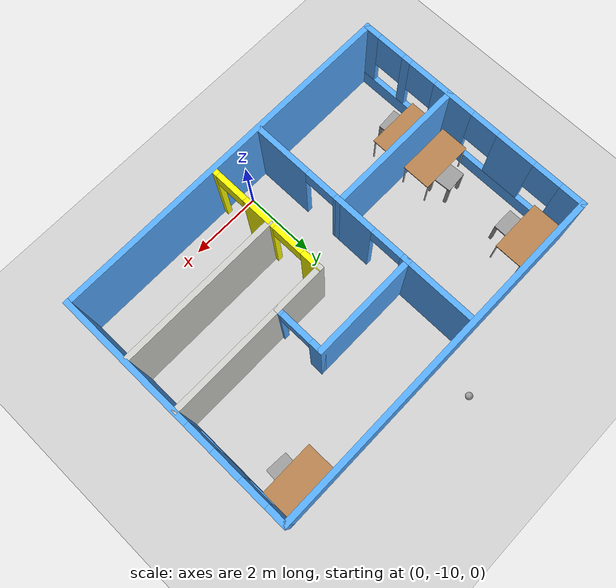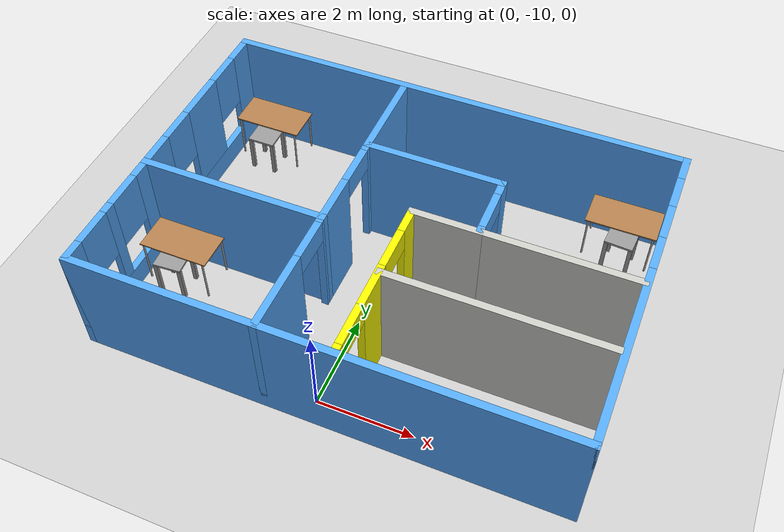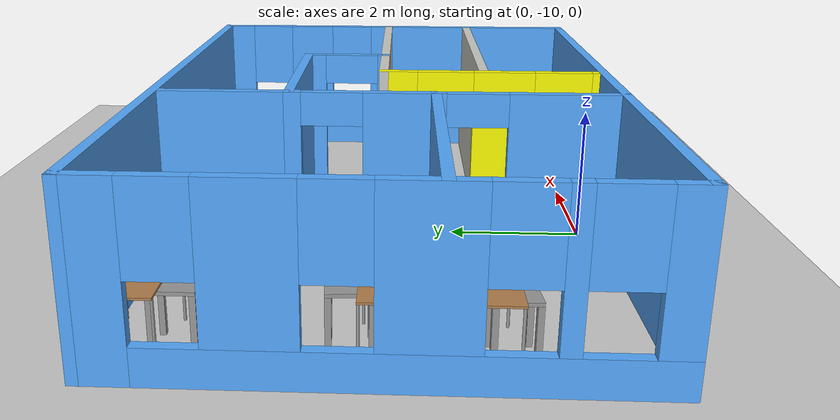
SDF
<sdf version="1.7">
 <world name="default">
  <plugin name="hello" filename="libhello.so"/>
  <light name="sun" type="directional">
   <pose>0 0 10 0 -0 0</pose>
   <diffuse>0.8 0.8 0.8 1</diffuse>
   <specular>0.2 0.2 0.2 1</specular>
   <attenuation>
    <range>1000</range>
    <constant>0.9</constant>
    <linear>0.01</linear>
    <quadratic>0.001</quadratic>
   </attenuation>
   <direction>-0.5 0.1 -0.9</direction>
   <spot><inner_angle>0</inner_angle><outer_angle>0</outer_angle><falloff>0</falloff></spot>
  </light>
  <model name="ground_plane">
   <static>1</static>
   <link name="link">
    <collision name="collision">
     <geometry><plane><normal>0 0 1</normal><size>100 100</size></plane></geometry>
     <surface>
      <contact><collide_bitmask>65535</collide_bitmask></contact>
      <friction><ode><mu>100</mu><mu2>50</mu2></ode></friction>
     </surface>
    </collision>
    <visual name="visual">
     <cast_shadows>0</cast_shadows>
     <geometry><plane><normal>0 0 1</normal><size>100 100</size></plane></geometry>
     <material>
      <script><uri>file://media/materials/scripts/gazebo.material</uri><name>Gazebo/Grey</name></script>
     </material>
    </visual>
   </link>
  </model>
  <gravity>0 0 -9.8</gravity>
  <magnetic_field>6e-06 2.3e-05 -4.2e-05</magnetic_field>
  <atmosphere type="adiabatic"/>
  <physics name="default_physics" default="0" type="ode">
   <max_step_size>0.001</max_step_size>
   <real_time_factor>1</real_time_factor>
   <real_time_update_rate>1000</real_time_update_rate>
  </physics>
  <scene><ambient>0.4 0.4 0.4 1</ambient><background>0.7 0.7 0.7 1</background><shadows>1</shadows></scene>
  <spherical_coordinates>
   <surface_model>EARTH_WGS84</surface_model>
   <latitude_deg>0</latitude_deg>
   <longitude_deg>0</longitude_deg>
   <elevation>0</elevation>
   <heading_deg>0</heading_deg>
  </spherical_coordinates>
  <model name="building">
   <pose>0.225 -6.955 0 0 -0 0</pose>
   <link name="Wall_13">
    <pose>-4.925 0 0 0 0 -1.5708</pose>
    <visual name="Wall_13_Visual_0">
     <pose>-3.1325 0 1.25 0 -0 0</pose>
     <geometry><box><size>0.735 0.15 2.5</size></box></geometry>
     <material>
      <script><uri>file://media/materials/scripts/gazebo.material</uri><name>Gazebo/Grey</name></script>
      <ambient>0.333333 0.666667 1 1</ambient>
     </material>
     <meta><layer>0</layer></meta>
    </visual>
    <collision name="Wall_13_Collision_0">
     <geometry><box><size>0.735 0.15 2.5</size></box></geometry>
     <pose>-3.1325 0 1.25 0 -0 0</pose>
    </collision>
    <visual name="Wall_13_Visual_1">
     <pose>0.3675 0 0.25 0 -0 0</pose>
     <geometry><box><size>6.265 0.15 0.5</size></box></geometry>
     <material>
      <script><uri>file://media/materials/scripts/gazebo.material</uri><name>Gazebo/Grey</name></script>
      <ambient>0.333333 0.666667 1 1</ambient>
     </material>
     <meta><layer>0</layer></meta>
    </visual>
    <collision name="Wall_13_Collision_1">
     <geometry><box><size>6.265 0.15 0.5</size></box></geometry>
     <pose>0.3675 0 0.25 0 -0 0</pose>
    </collision>
    <visual name="Wall_13_Visual_2">
     <pose>-1.405 0 1.5 0 -0 0</pose>
     <geometry><box><size>1.12 0.15 2</size></box></geometry>
     <material>
      <script><uri>file://media/materials/scripts/gazebo.material</uri><name>Gazebo/Grey</name></script>
      <ambient>0.333333 0.666667 1 1</ambient>
     </material>
     <meta><layer>0</layer></meta>
    </visual>
    <collision name="Wall_13_Collision_2">
     <geometry><box><size>1.12 0.15 2</size></box></geometry>
     <pose>-1.405 0 1.5 0 -0 0</pose>
    </collision>
    <visual name="Wall_13_Visual_3">
     <pose>0.555 0 1.5 0 -0 0</pose>
     <geometry><box><size>1.2 0.15 2</size></box></geometry>
     <material>
      <script><uri>file://media/materials/scripts/gazebo.material</uri><name>Gazebo/Grey</name></script>
      <ambient>0.333333 0.666667 1 1</ambient>
     </material>
     <meta><layer>0</layer></meta>
    </visual>
    <collision name="Wall_13_Collision_3">
     <geometry><box><size>1.2 0.15 2</size></box></geometry>
     <pose>0.555 0 1.5 0 -0 0</pose>
    </collision>
    <visual name="Wall_13_Visual_4">
     <pose>2.08 0 1.5 0 -0 0</pose>
     <geometry><box><size>0.25 0.15 2</size></box></geometry>
     <material>
      <script><uri>file://media/materials/scripts/gazebo.material</uri><name>Gazebo/Grey</name></script>
      <ambient>0.333333 0.666667 1 1</ambient>
     </material>
     <meta><layer>0</layer></meta>
    </visual>
    <collision name="Wall_13_Collision_4">
     <geometry><box><size>0.25 0.15 2</size></box></geometry>
     <pose>2.08 0 1.5 0 -0 0</pose>
    </collision>
    <visual name="Wall_13_Visual_5">
     <pose>3.2525 0 1.5 0 -0 0</pose>
     <geometry><box><size>0.495 0.15 2</size></box></geometry>
     <material>
      <script><uri>file://media/materials/scripts/gazebo.material</uri><name>Gazebo/Grey</name></script>
      <ambient>0.333333 0.666667 1 1</ambient>
     </material>
     <meta><layer>0</layer></meta>
    </visual>
    <collision name="Wall_13_Collision_5">
     <geometry><box><size>0.495 0.15 2</size></box></geometry>
     <pose>3.2525 0 1.5 0 -0 0</pose>
    </collision>
    <visual name="Wall_13_Visual_6">
     <pose>-2.365 0 1.9 0 -0 0</pose>
     <geometry><box><size>0.8 0.15 1.2</size></box></geometry>
     <material>
      <script><uri>file://media/materials/scripts/gazebo.material</uri><name>Gazebo/Grey</name></script>
      <ambient>0.333333 0.666667 1 1</ambient>
     </material>
     <meta><layer>0</layer></meta>
    </visual>
    <collision name="Wall_13_Collision_6">
     <geometry><box><size>0.8 0.15 1.2</size></box></geometry>
     <pose>-2.365 0 1.9 0 -0 0</pose>
    </collision>
    <visual name="Wall_13_Visual_7">
     <pose>-0.445 0 1.9 0 -0 0</pose>
     <geometry><box><size>0.8 0.15 1.2</size></box></geometry>
     <material>
      <script><uri>file://media/materials/scripts/gazebo.material</uri><name>Gazebo/Grey</name></script>
      <ambient>0.333333 0.666667 1 1</ambient>
     </material>
     <meta><layer>0</layer></meta>
    </visual>
    <collision name="Wall_13_Collision_7">
     <geometry><box><size>0.8 0.15 1.2</size></box></geometry>
     <pose>-0.445 0 1.9 0 -0 0</pose>
    </collision>
    <visual name="Wall_13_Visual_8">
     <pose>1.555 0 1.9 0 -0 0</pose>
     <geometry><box><size>0.8 0.15 1.2</size></box></geometry>
     <material>
      <script><uri>file://media/materials/scripts/gazebo.material</uri><name>Gazebo/Grey</name></script>
      <ambient>0.333333 0.666667 1 1</ambient>
     </material>
     <meta><layer>0</layer></meta>
    </visual>
    <collision name="Wall_13_Collision_8">
     <geometry><box><size>0.8 0.15 1.2</size></box></geometry>
     <pose>1.555 0 1.9 0 -0 0</pose>
    </collision>
    <visual name="Wall_13_Visual_9">
     <pose>2.605 0 1.9 0 -0 0</pose>
     <geometry><box><size>0.8 0.15 1.2</size></box></geometry>
     <material>
      <script><uri>file://media/materials/scripts/gazebo.material</uri><name>Gazebo/Grey</name></script>
      <ambient>0.333333 0.666667 1 1</ambient>
     </material>
     <meta><layer>0</layer></meta>
    </visual>
    <collision name="Wall_13_Collision_9">
     <geometry><box><size>0.8 0.15 1.2</size></box></geometry>
     <pose>2.605 0 1.9 0 -0 0</pose>
    </collision>
   </link>
   <link name="Wall_14">
    <collision name="Wall_14_Collision">
     <geometry><box><size>10 0.15 2.5</size></box></geometry>
     <pose>0 0 1.25 0 -0 0</pose>
    </collision>
    <visual name="Wall_14_Visual">
     <pose>0 0 1.25 0 -0 0</pose>
     <geometry><box><size>10 0.15 2.5</size></box></geometry>
     <material>
      <script><uri>file://media/materials/scripts/gazebo.material</uri><name>Gazebo/Grey</name></script>
      <ambient>0.333333 0.666667 1 1</ambient>
     </material>
     <meta><layer>0</layer></meta>
    </visual>
    <pose>0 -3.425 0 0 -0 0</pose>
   </link>
   <link name="Wall_15">
    <pose>4.925 0 0 0 -0 1.5708</pose>
    <visual name="Wall_15_Visual_0">
     <pose>-1.5275 0 1.25 0 -0 0</pose>
     <geometry><box><size>3.945 0.15 2.5</size></box></geometry>
     <material>
      <script><uri>file://media/materials/scripts/gazebo.material</uri><name>Gazebo/Grey</name></script>
      <ambient>0.333333 0.666667 1 1</ambient>
     </material>
     <meta><layer>0</layer></meta>
    </visual>
    <collision name="Wall_15_Collision_0">
     <geometry><box><size>3.945 0.15 2.5</size></box></geometry>
     <pose>-1.5275 0 1.25 0 -0 0</pose>
    </collision>
    <visual name="Wall_15_Visual_1">
     <pose>1.9725 0 0.25 0 -0 0</pose>
     <geometry><box><size>3.055 0.15 0.5</size></box></geometry>
     <material>
      <script><uri>file://media/materials/scripts/gazebo.material</uri><name>Gazebo/Grey</name></script>
      <ambient>0.333333 0.666667 1 1</ambient>
     </material>
     <meta><layer>0</layer></meta>
    </visual>
    <collision name="Wall_15_Collision_1">
     <geometry><box><size>3.055 0.15 0.5</size></box></geometry>
     <pose>1.9725 0 0.25 0 -0 0</pose>
    </collision>
    <visual name="Wall_15_Visual_2">
     <pose>1.67 0 1.5 0 -0 0</pose>
     <geometry><box><size>0.85 0.15 2</size></box></geometry>
     <material>
      <script><uri>file://media/materials/scripts/gazebo.material</uri><name>Gazebo/Grey</name></script>
      <ambient>0.333333 0.666667 1 1</ambient>
     </material>
     <meta><layer>0</layer></meta>
    </visual>
    <collision name="Wall_15_Collision_2">
     <geometry><box><size>0.85 0.15 2</size></box></geometry>
     <pose>1.67 0 1.5 0 -0 0</pose>
    </collision>
    <visual name="Wall_15_Visual_3">
     <pose>3.1975 0 1.5 0 -0 0</pose>
     <geometry><box><size>0.605 0.15 2</size></box></geometry>
     <material>
      <script><uri>file://media/materials/scripts/gazebo.material</uri><name>Gazebo/Grey</name></script>
      <ambient>0.333333 0.666667 1 1</ambient>
     </material>
     <meta><layer>0</layer></meta>
    </visual>
    <collision name="Wall_15_Collision_3">
     <geometry><box><size>0.605 0.15 2</size></box></geometry>
     <pose>3.1975 0 1.5 0 -0 0</pose>
    </collision>
    <visual name="Wall_15_Visual_4">
     <pose>0.845 0 1.9 0 -0 0</pose>
     <geometry><box><size>0.8 0.15 1.2</size></box></geometry>
     <material>
      <script><uri>file://media/materials/scripts/gazebo.material</uri><name>Gazebo/Grey</name></script>
      <ambient>0.333333 0.666667 1 1</ambient>
     </material>
     <meta><layer>0</layer></meta>
    </visual>
    <collision name="Wall_15_Collision_4">
     <geometry><box><size>0.8 0.15 1.2</size></box></geometry>
     <pose>0.845 0 1.9 0 -0 0</pose>
    </collision>
    <visual name="Wall_15_Visual_5">
     <pose>2.495 0 1.9 0 -0 0</pose>
     <geometry><box><size>0.8 0.15 1.2</size></box></geometry>
     <material>
      <script><uri>file://media/materials/scripts/gazebo.material</uri><name>Gazebo/Grey</name></script>
      <ambient>0.333333 0.666667 1 1</ambient>
     </material>
     <meta><layer>0</layer></meta>
    </visual>
    <collision name="Wall_15_Collision_5">
     <geometry><box><size>0.8 0.15 1.2</size></box></geometry>
     <pose>2.495 0 1.9 0 -0 0</pose>
    </collision>
   </link>
   <link name="Wall_16">
    <collision name="Wall_16_Collision">
     <geometry><box><size>10 0.15 2.5</size></box></geometry>
     <pose>0 0 1.25 0 -0 0</pose>
    </collision>
    <visual name="Wall_16_Visual">
     <pose>0 0 1.25 0 -0 0</pose>
     <geometry><box><size>10 0.15 2.5</size></box></geometry>
     <material>
      <script><uri>file://media/materials/scripts/gazebo.material</uri><name>Gazebo/Grey</name></script>
      <ambient>0.333333 0.666667 1 1</ambient>
     </material>
     <meta><layer>0</layer></meta>
    </visual>
    <pose>0 3.425 0 0 -0 3.14159</pose>
   </link>
   <link name="Wall_26">
    <pose>-1.075 -1 0 0 -0 1.5708</pose>
    <visual name="Wall_26_Visual_0">
     <pose>-1.6325 0 1.25 0 -0 0</pose>
     <geometry><box><size>1.735 0.15 2.5</size></box></geometry>
     <material>
      <script><uri>file://media/materials/scripts/gazebo.material</uri><name>Gazebo/Grey</name></script>
      <ambient>0.333333 0.666667 1 1</ambient>
     </material>
     <meta><layer>0</layer></meta>
    </visual>
    <collision name="Wall_26_Collision_0">
     <geometry><box><size>1.735 0.15 2.5</size></box></geometry>
     <pose>-1.6325 0 1.25 0 -0 0</pose>
    </collision>
    <visual name="Wall_26_Visual_1">
     <pose>0.74 0 1.25 0 -0 0</pose>
     <geometry><box><size>1.21 0.15 2.5</size></box></geometry>
     <material>
      <script><uri>file://media/materials/scripts/gazebo.material</uri><name>Gazebo/Grey</name></script>
      <ambient>0.333333 0.666667 1 1</ambient>
     </material>
     <meta><layer>0</layer></meta>
    </visual>
    <collision name="Wall_26_Collision_1">
     <geometry><box><size>1.21 0.15 2.5</size></box></geometry>
     <pose>0.74 0 1.25 0 -0 0</pose>
    </collision>
    <visual name="Wall_26_Visual_2">
     <pose>2.3725 0 1.25 0 -0 0</pose>
     <geometry><box><size>0.255 0.15 2.5</size></box></geometry>
     <material>
      <script><uri>file://media/materials/scripts/gazebo.material</uri><name>Gazebo/Grey</name></script>
      <ambient>0.333333 0.666667 1 1</ambient>
     </material>
     <meta><layer>0</layer></meta>
    </visual>
    <collision name="Wall_26_Collision_2">
     <geometry><box><size>0.255 0.15 2.5</size></box></geometry>
     <pose>2.3725 0 1.25 0 -0 0</pose>
    </collision>
    <visual name="Wall_26_Visual_3">
     <pose>-0.315001 0 2.25 0 -0 0</pose>
     <geometry><box><size>0.9 0.15 0.5</size></box></geometry>
     <material>
      <script><uri>file://media/materials/scripts/gazebo.material</uri><name>Gazebo/Grey</name></script>
      <ambient>0.333333 0.666667 1 1</ambient>
     </material>
     <meta><layer>0</layer></meta>
    </visual>
    <collision name="Wall_26_Collision_3">
     <geometry><box><size>0.9 0.15 0.5</size></box></geometry>
     <pose>-0.315001 0 2.25 0 -0 0</pose>
    </collision>
    <visual name="Wall_26_Visual_4">
     <pose>1.795 0 2.25 0 -0 0</pose>
     <geometry><box><size>0.9 0.15 0.5</size></box></geometry>
     <material>
      <script><uri>file://media/materials/scripts/gazebo.material</uri><name>Gazebo/Grey</name></script>
      <ambient>0.333333 0.666667 1 1</ambient>
     </material>
     <meta><layer>0</layer></meta>
    </visual>
    <collision name="Wall_26_Collision_4">
     <geometry><box><size>0.9 0.15 0.5</size></box></geometry>
     <pose>1.795 0 2.25 0 -0 0</pose>
    </collision>
   </link>
   <link name="Wall_29">
    <collision name="Wall_29_Collision">
     <geometry><box><size>1.5 0.15 2.5</size></box></geometry>
     <pose>0 0 1.25 0 -0 0</pose>
    </collision>
    <visual name="Wall_29_Visual">
     <pose>0 0 1.25 0 -0 0</pose>
     <geometry><box><size>1.5 0.15 2.5</size></box></geometry>
     <material>
      <script><uri>file://media/materials/scripts/gazebo.material</uri><name>Gazebo/CeilingTiled</name></script>
      <ambient>1 1 0 1</ambient>
     </material>
     <meta><layer>0</layer></meta>
    </visual>
    <pose>1.1 0.075 0 0 -0 3.14159</pose>
   </link>
   <link name="Wall_30">
    <pose>0.425 -1.6 0 0 0 -1.5708</pose>
    <visual name="Wall_30_Visual_0">
     <pose>-1.4425 0 1.25 0 -0 0</pose>
     <geometry><box><size>0.615 0.15 2.5</size></box></geometry>
     <material>
      <script><uri>file://media/materials/scripts/gazebo.material</uri><name>Gazebo/Grey</name></script>
      <ambient>1 1 0 1</ambient>
     </material>
     <meta><layer>0</layer></meta>
    </visual>
    <collision name="Wall_30_Collision_0">
     <geometry><box><size>0.615 0.15 2.5</size></box></geometry>
     <pose>-1.4425 0 1.25 0 -0 0</pose>
    </collision>
    <visual name="Wall_30_Visual_1">
     <pose>0.25 0 1.25 0 -0 0</pose>
     <geometry><box><size>0.97 0.15 2.5</size></box></geometry>
     <material>
      <script><uri>file://media/materials/scripts/gazebo.material</uri><name>Gazebo/Grey</name></script>
      <ambient>1 1 0 1</ambient>
     </material>
     <meta><layer>0</layer></meta>
    </visual>
    <collision name="Wall_30_Collision_1">
     <geometry><box><size>0.97 0.15 2.5</size></box></geometry>
     <pose>0.25 0 1.25 0 -0 0</pose>
    </collision>
    <visual name="Wall_30_Visual_2">
     <pose>1.6925 0 1.25 0 -0 0</pose>
     <geometry><box><size>0.115001 0.15 2.5</size></box></geometry>
     <material>
      <script><uri>file://media/materials/scripts/gazebo.material</uri><name>Gazebo/Grey</name></script>
      <ambient>1 1 0 1</ambient>
     </material>
     <meta><layer>0</layer></meta>
    </visual>
    <collision name="Wall_30_Collision_2">
     <geometry><box><size>0.115001 0.15 2.5</size></box></geometry>
     <pose>1.6925 0 1.25 0 -0 0</pose>
    </collision>
    <visual name="Wall_30_Visual_3">
     <pose>-0.685 0 2.25 0 -0 0</pose>
     <geometry><box><size>0.9 0.15 0.5</size></box></geometry>
     <material>
      <script><uri>file://media/materials/scripts/gazebo.material</uri><name>Gazebo/Grey</name></script>
      <ambient>1 1 0 1</ambient>
     </material>
     <meta><layer>0</layer></meta>
    </visual>
    <collision name="Wall_30_Collision_3">
     <geometry><box><size>0.9 0.15 0.5</size></box></geometry>
     <pose>-0.685 0 2.25 0 -0 0</pose>
    </collision>
    <visual name="Wall_30_Visual_4">
     <pose>1.185 0 2.25 0 -0 0</pose>
     <geometry><box><size>0.9 0.15 0.5</size></box></geometry>
     <material>
      <script><uri>file://media/materials/scripts/gazebo.material</uri><name>Gazebo/Grey</name></script>
      <ambient>1 1 0 1</ambient>
     </material>
     <meta><layer>0</layer></meta>
    </visual>
    <collision name="Wall_30_Collision_4">
     <geometry><box><size>0.9 0.15 0.5</size></box></geometry>
     <pose>1.185 0 2.25 0 -0 0</pose>
    </collision>
   </link>
   <link name="Wall_32">
    <collision name="Wall_32_Collision">
     <geometry><box><size>4 0.15 2.5</size></box></geometry>
     <pose>0 0 1.25 0 -0 0</pose>
    </collision>
    <visual name="Wall_32_Visual">
     <pose>0 0 1.25 0 -0 0</pose>
     <geometry><box><size>4 0.15 2.5</size></box></geometry>
     <material>
      <script><uri>file://media/materials/scripts/gazebo.material</uri><name>Gazebo/Grey</name></script>
      <ambient>0.333333 0.666667 1 1</ambient>
     </material>
     <meta><layer>0</layer></meta>
    </visual>
    <pose>-3 -0.715 0 0 -0 3.14159</pose>
   </link>
   <link name="Wall_41">
    <collision name="Wall_41_Collision">
     <geometry><box><size>3 0.15 2.5</size></box></geometry>
     <pose>0 0 1.25 0 -0 0</pose>
    </collision>
    <visual name="Wall_41_Visual">
     <pose>0 0 1.25 0 -0 0</pose>
     <geometry><box><size>3 0.15 2.5</size></box></geometry>
     <material>
      <script><uri>file://media/materials/scripts/gazebo.material</uri><name>Gazebo/Grey</name></script>
      <ambient>0.333333 0.666667 1 1</ambient>
     </material>
     <meta><layer>0</layer></meta>
    </visual>
    <pose>0.35 1.425 0 0 -0 0</pose>
   </link>
   <link name="Wall_42">
    <pose>1.775 0.75 0 0 0 -1.5708</pose>
    <visual name="Wall_42_Visual_0">
     <pose>-0.5575 0 1.25 0 -0 0</pose>
     <geometry><box><size>0.385 0.15 2.5</size></box></geometry>
     <material>
      <script><uri>file://media/materials/scripts/gazebo.material</uri><name>Gazebo/Grey</name></script>
      <ambient>0.333333 0.666667 1 1</ambient>
     </material>
     <meta><layer>0</layer></meta>
    </visual>
    <collision name="Wall_42_Collision_0">
     <geometry><box><size>0.385 0.15 2.5</size></box></geometry>
     <pose>-0.5575 0 1.25 0 -0 0</pose>
    </collision>
    <visual name="Wall_42_Visual_1">
     <pose>0.6425 0 1.25 0 -0 0</pose>
     <geometry><box><size>0.215 0.15 2.5</size></box></geometry>
     <material>
      <script><uri>file://media/materials/scripts/gazebo.material</uri><name>Gazebo/Grey</name></script>
      <ambient>0.333333 0.666667 1 1</ambient>
     </material>
     <meta><layer>0</layer></meta>
    </visual>
    <collision name="Wall_42_Collision_1">
     <geometry><box><size>0.215 0.15 2.5</size></box></geometry>
     <pose>0.6425 0 1.25 0 -0 0</pose>
    </collision>
    <visual name="Wall_42_Visual_2">
     <pose>0.085 0 2.25 0 -0 0</pose>
     <geometry><box><size>0.9 0.15 0.5</size></box></geometry>
     <material>
      <script><uri>file://media/materials/scripts/gazebo.material</uri><name>Gazebo/Grey</name></script>
      <ambient>0.333333 0.666667 1 1</ambient>
     </material>
     <meta><layer>0</layer></meta>
    </visual>
    <collision name="Wall_42_Collision_2">
     <geometry><box><size>0.9 0.15 0.5</size></box></geometry>
     <pose>0.085 0 2.25 0 -0 0</pose>
    </collision>
   </link>
   <link name="Wall_46">
    <collision name="Wall_46_Collision">
     <geometry><box><size>2 0.15 2.5</size></box></geometry>
     <pose>0 0 1.25 0 -0 0</pose>
    </collision>
    <visual name="Wall_46_Visual">
     <pose>0 0 1.25 0 -0 0</pose>
     <geometry><box><size>2 0.15 2.5</size></box></geometry>
     <material>
      <script><uri>file://media/materials/scripts/gazebo.material</uri><name>Gazebo/Grey</name></script>
      <ambient>0.333333 0.666667 1 1</ambient>
     </material>
     <meta><layer>0</layer></meta>
    </visual>
    <pose>-1.075 2.35 0 0 -0 1.5708</pose>
   </link>
   <link name="Wall_48">
    <collision name="Wall_48_Collision">
     <geometry><box><size>3.25 0.15 2.5</size></box></geometry>
     <pose>0 0 1.25 0 -0 0</pose>
    </collision>
    <visual name="Wall_48_Visual">
     <pose>0 0 1.25 0 -0 0</pose>
     <geometry><box><size>3.25 0.15 2.5</size></box></geometry>
     <material>
      <script><uri>file://media/materials/scripts/gazebo.material</uri><name>Gazebo/CeilingTiled</name></script>
      <ambient>1 1 0 1</ambient>
     </material>
     <meta><layer>0</layer></meta>
    </visual>
    <pose>3.325 0.075 0 0 -0 0</pose>
   </link>
   <link name="Wall_54">
    <collision name="Wall_54_Collision">
     <geometry><box><size>4.5 0.15 2.5</size></box></geometry>
     <pose>0 0 1.25 0 -0 0</pose>
    </collision>
    <visual name="Wall_54_Visual">
     <pose>0 0 1.25 0 -0 0</pose>
     <geometry><box><size>4.5 0.15 2.5</size></box></geometry>
     <material>
      <script><uri>file://media/materials/scripts/gazebo.material</uri><name>Gazebo/CeilingTiled</name></script>
      <ambient>1 1 0 1</ambient>
     </material>
     <meta><layer>0</layer></meta>
    </visual>
    <pose>2.63 -1.525 0 0 -0 0</pose>
   </link>
   <static>1</static>
  </model>
  <model name="table">
   <static>1</static>
   <link name="link">
    <collision name="surface">
     <pose>0 0 1 0 -0 0</pose>
     <geometry><box><size>1.5 0.8 0.03</size></box></geometry>
     <surface><friction><ode><mu>0.6</mu><mu2>0.6</mu2></ode></friction></surface>
    </collision>
    <visual name="visual1">
     <pose>0 0 1 0 -0 0</pose>
     <geometry><box><size>1.5 0.8 0.03</size></box></geometry>
     <material>
      <script><uri>file://media/materials/scripts/gazebo.material</uri><name>Gazebo/Wood</name></script>
     </material>
    </visual>
    <collision name="front_left_leg">
     <pose>0.68 0.38 0.5 0 -0 0</pose>
     <geometry><cylinder><radius>0.02</radius><length>1</length></cylinder></geometry>
    </collision>
    <visual name="front_left_leg">
     <pose>0.68 0.38 0.5 0 -0 0</pose>
     <geometry><cylinder><radius>0.02</radius><length>1</length></cylinder></geometry>
     <material>
      <script><uri>file://media/materials/scripts/gazebo.material</uri><name>Gazebo/Grey</name></script>
     </material>
    </visual>
    <collision name="front_right_leg">
     <pose>0.68 -0.38 0.5 0 -0 0</pose>
     <geometry><cylinder><radius>0.02</radius><length>1</length></cylinder></geometry>
    </collision>
    <visual name="front_right_leg">
     <pose>0.68 -0.38 0.5 0 -0 0</pose>
     <geometry><cylinder><radius>0.02</radius><length>1</length></cylinder></geometry>
     <material>
      <script><uri>file://media/materials/scripts/gazebo.material</uri><name>Gazebo/Grey</name></script>
     </material>
    </visual>
    <collision name="back_right_leg">
     <pose>-0.68 -0.38 0.5 0 -0 0</pose>
     <geometry><cylinder><radius>0.02</radius><length>1</length></cylinder></geometry>
    </collision>
    <visual name="back_right_leg">
     <pose>-0.68 -0.38 0.5 0 -0 0</pose>
     <geometry><cylinder><radius>0.02</radius><length>1</length></cylinder></geometry>
     <material>
      <script><uri>file://media/materials/scripts/gazebo.material</uri><name>Gazebo/Grey</name></script>
     </material>
    </visual>
    <collision name="back_left_leg">
     <pose>-0.68 0.38 0.5 0 -0 0</pose>
     <geometry><cylinder><radius>0.02</radius><length>1</length></cylinder></geometry>
    </collision>
    <visual name="back_left_leg">
     <pose>-0.68 0.38 0.5 0 -0 0</pose>
     <geometry><cylinder><radius>0.02</radius><length>1</length></cylinder></geometry>
     <material>
      <script><uri>file://media/materials/scripts/gazebo.material</uri><name>Gazebo/Grey</name></script>
     </material>
    </visual>
   </link>
   <pose>-3.83942 -4.04953 0 0 -0 0</pose>
  </model>
  <model name="table_0">
   <static>1</static>
   <link name="link">
    <collision name="surface">
     <pose>0 0 1 0 -0 0</pose>
     <geometry><box><size>1.5 0.8 0.03</size></box></geometry>
     <surface><friction><ode><mu>0.6</mu><mu2>0.6</mu2></ode></friction></surface>
    </collision>
    <visual name="visual1">
     <pose>0 0 1 0 -0 0</pose>
     <geometry><box><size>1.5 0.8 0.03</size></box></geometry>
     <material>
      <script><uri>file://media/materials/scripts/gazebo.material</uri><name>Gazebo/Wood</name></script>
     </material>
    </visual>
    <collision name="front_left_leg">
     <pose>0.68 0.38 0.5 0 -0 0</pose>
     <geometry><cylinder><radius>0.02</radius><length>1</length></cylinder></geometry>
    </collision>
    <visual name="front_left_leg">
     <pose>0.68 0.38 0.5 0 -0 0</pose>
     <geometry><cylinder><radius>0.02</radius><length>1</length></cylinder></geometry>
     <material>
      <script><uri>file://media/materials/scripts/gazebo.material</uri><name>Gazebo/Grey</name></script>
     </material>
    </visual>
    <collision name="front_right_leg">
     <pose>0.68 -0.38 0.5 0 -0 0</pose>
     <geometry><cylinder><radius>0.02</radius><length>1</length></cylinder></geometry>
    </collision>
    <visual name="front_right_leg">
     <pose>0.68 -0.38 0.5 0 -0 0</pose>
     <geometry><cylinder><radius>0.02</radius><length>1</length></cylinder></geometry>
     <material>
      <script><uri>file://media/materials/scripts/gazebo.material</uri><name>Gazebo/Grey</name></script>
     </material>
    </visual>
    <collision name="back_right_leg">
     <pose>-0.68 -0.38 0.5 0 -0 0</pose>
     <geometry><cylinder><radius>0.02</radius><length>1</length></cylinder></geometry>
    </collision>
    <visual name="back_right_leg">
     <pose>-0.68 -0.38 0.5 0 -0 0</pose>
     <geometry><cylinder><radius>0.02</radius><length>1</length></cylinder></geometry>
     <material>
      <script><uri>file://media/materials/scripts/gazebo.material</uri><name>Gazebo/Grey</name></script>
     </material>
    </visual>
    <collision name="back_left_leg">
     <pose>-0.68 0.38 0.5 0 -0 0</pose>
     <geometry><cylinder><radius>0.02</radius><length>1</length></cylinder></geometry>
    </collision>
    <visual name="back_left_leg">
     <pose>-0.68 0.38 0.5 0 -0 0</pose>
     <geometry><cylinder><radius>0.02</radius><length>1</length></cylinder></geometry>
     <material>
      <script><uri>file://media/materials/scripts/gazebo.material</uri><name>Gazebo/Grey</name></script>
     </material>
    </visual>
   </link>
   <pose>-3.83019 -7.10717 0 0 -0 0</pose>
  </model>
  <model name="table_1">
   <static>1</static>
   <link name="link">
    <collision name="surface">
     <pose>0 0 1 0 -0 0</pose>
     <geometry><box><size>1.5 0.8 0.03</size></box></geometry>
     <surface><friction><ode><mu>0.6</mu><mu2>0.6</mu2></ode></friction></surface>
    </collision>
    <visual name="visual1">
     <pose>0 0 1 0 -0 0</pose>
     <geometry><box><size>1.5 0.8 0.03</size></box></geometry>
     <material>
      <script><uri>file://media/materials/scripts/gazebo.material</uri><name>Gazebo/Wood</name></script>
     </material>
    </visual>
    <collision name="front_left_leg">
     <pose>0.68 0.38 0.5 0 -0 0</pose>
     <geometry><cylinder><radius>0.02</radius><length>1</length></cylinder></geometry>
    </collision>
    <visual name="front_left_leg">
     <pose>0.68 0.38 0.5 0 -0 0</pose>
     <geometry><cylinder><radius>0.02</radius><length>1</length></cylinder></geometry>
     <material>
      <script><uri>file://media/materials/scripts/gazebo.material</uri><name>Gazebo/Grey</name></script>
     </material>
    </visual>
    <collision name="front_right_leg">
     <pose>0.68 -0.38 0.5 0 -0 0</pose>
     <geometry><cylinder><radius>0.02</radius><length>1</length></cylinder></geometry>
    </collision>
    <visual name="front_right_leg">
     <pose>0.68 -0.38 0.5 0 -0 0</pose>
     <geometry><cylinder><radius>0.02</radius><length>1</length></cylinder></geometry>
     <material>
      <script><uri>file://media/materials/scripts/gazebo.material</uri><name>Gazebo/Grey</name></script>
     </material>
    </visual>
    <collision name="back_right_leg">
     <pose>-0.68 -0.38 0.5 0 -0 0</pose>
     <geometry><cylinder><radius>0.02</radius><length>1</length></cylinder></geometry>
    </collision>
    <visual name="back_right_leg">
     <pose>-0.68 -0.38 0.5 0 -0 0</pose>
     <geometry><cylinder><radius>0.02</radius><length>1</length></cylinder></geometry>
     <material>
      <script><uri>file://media/materials/scripts/gazebo.material</uri><name>Gazebo/Grey</name></script>
     </material>
    </visual>
    <collision name="back_left_leg">
     <pose>-0.68 0.38 0.5 0 -0 0</pose>
     <geometry><cylinder><radius>0.02</radius><length>1</length></cylinder></geometry>
    </collision>
    <visual name="back_left_leg">
     <pose>-0.68 0.38 0.5 0 -0 0</pose>
     <geometry><cylinder><radius>0.02</radius><length>1</length></cylinder></geometry>
     <material>
      <script><uri>file://media/materials/scripts/gazebo.material</uri><name>Gazebo/Grey</name></script>
     </material>
    </visual>
   </link>
   <pose>-3.83908 -8.17845 0 0 -0 0</pose>
  </model>
  <model name="table_2">
   <static>1</static>
   <link name="link">
    <collision name="surface">
     <pose>0 0 1 0 -0 0</pose>
     <geometry><box><size>1.5 0.8 0.03</size></box></geometry>
     <surface><friction><ode><mu>0.6</mu><mu2>0.6</mu2></ode></friction></surface>
    </collision>
    <visual name="visual1">
     <pose>0 0 1 0 -0 0</pose>
     <geometry><box><size>1.5 0.8 0.03</size></box></geometry>
     <material>
      <script><uri>file://media/materials/scripts/gazebo.material</uri><name>Gazebo/Wood</name></script>
     </material>
    </visual>
    <collision name="front_left_leg">
     <pose>0.68 0.38 0.5 0 -0 0</pose>
     <geometry><cylinder><radius>0.02</radius><length>1</length></cylinder></geometry>
    </collision>
    <visual name="front_left_leg">
     <pose>0.68 0.38 0.5 0 -0 0</pose>
     <geometry><cylinder><radius>0.02</radius><length>1</length></cylinder></geometry>
     <material>
      <script><uri>file://media/materials/scripts/gazebo.material</uri><name>Gazebo/Grey</name></script>
     </material>
    </visual>
    <collision name="front_right_leg">
     <pose>0.68 -0.38 0.5 0 -0 0</pose>
     <geometry><cylinder><radius>0.02</radius><length>1</length></cylinder></geometry>
    </collision>
    <visual name="front_right_leg">
     <pose>0.68 -0.38 0.5 0 -0 0</pose>
     <geometry><cylinder><radius>0.02</radius><length>1</length></cylinder></geometry>
     <material>
      <script><uri>file://media/materials/scripts/gazebo.material</uri><name>Gazebo/Grey</name></script>
     </material>
    </visual>
    <collision name="back_right_leg">
     <pose>-0.68 -0.38 0.5 0 -0 0</pose>
     <geometry><cylinder><radius>0.02</radius><length>1</length></cylinder></geometry>
    </collision>
    <visual name="back_right_leg">
     <pose>-0.68 -0.38 0.5 0 -0 0</pose>
     <geometry><cylinder><radius>0.02</radius><length>1</length></cylinder></geometry>
     <material>
      <script><uri>file://media/materials/scripts/gazebo.material</uri><name>Gazebo/Grey</name></script>
     </material>
    </visual>
    <collision name="back_left_leg">
     <pose>-0.68 0.38 0.5 0 -0 0</pose>
     <geometry><cylinder><radius>0.02</radius><length>1</length></cylinder></geometry>
    </collision>
    <visual name="back_left_leg">
     <pose>-0.68 0.38 0.5 0 -0 0</pose>
     <geometry><cylinder><radius>0.02</radius><length>1</length></cylinder></geometry>
     <material>
      <script><uri>file://media/materials/scripts/gazebo.material</uri><name>Gazebo/Grey</name></script>
     </material>
    </visual>
   </link>
   <pose>4.30856 -4.0322 0 0 -0 0</pose>
  </model>
  <model name="seat">
   <link name="link_0">
    <pose>0 0 0.34 0 -0 0</pose>
    <inertial>
     <mass>1</mass>
     <inertia>
      <ixx>0.166667</ixx>
      <ixy>0</ixy>
      <ixz>0</ixz>
      <iyy>0.166667</iyy>
      <iyz>0</iyz>
      <izz>0.166667</izz>
     </inertia>
    </inertial>
    <kinematic>1</kinematic>
    <visual name="visual">
     <geometry><box><size>0.6 0.6 0.05</size></box></geometry>
     <material>
      <lighting>1</lighting>
      <script><uri>file://media/materials/scripts/gazebo.material</uri><name>Gazebo/Grey</name></script>
      <shader type="pixel"><normal_map>__default__</normal_map></shader>
      <ambient>0.3 0.3 0.3 1</ambient>
      <diffuse>0.7 0.7 0.7 1</diffuse>
      <specular>0.01 0.01 0.01 1</specular>
      <emissive>0 0 0 1</emissive>
     </material>
    </visual>
    <collision name="collision">
     <geometry><box><size>0.6 0.6 0.05</size></box></geometry>
     <surface>
      <friction>
       <ode><mu>1</mu><mu2>1</mu2><fdir1>0 0 0</fdir1><slip1>0</slip1><slip2>0</slip2></ode>
       <torsional>
        <coefficient>1</coefficient>
        <patch_radius>0</patch_radius>
        <surface_radius>0</surface_radius>
        <use_patch_radius>1</use_patch_radius>
        <ode><slip>0</slip></ode>
       </torsional>
      </friction>
      <bounce><restitution_coefficient>0</restitution_coefficient><threshold>1e+06</threshold></bounce>
      <contact>
       <collide_without_contact>0</collide_without_contact>
       <collide_without_contact_bitmask>1</collide_without_contact_bitmask>
       <collide_bitmask>1</collide_bitmask>
       <ode>
        <soft_cfm>0</soft_cfm>
        <soft_erp>0.2</soft_erp>
        <kp>1e+13</kp>
        <kd>1</kd>
        <max_vel>0.01</max_vel>
        <min_depth>0</min_depth>
       </ode>
       <bullet>
        <split_impulse>1</split_impulse>
        <split_impulse_penetration_threshold>-0.01</split_impulse_penetration_threshold>
        <soft_cfm>0</soft_cfm>
        <soft_erp>0.2</soft_erp>
        <kp>1e+13</kp>
        <kd>1</kd>
       </bullet>
      </contact>
     </surface>
    </collision>
   </link>
   <link name="link_1">
    <pose>-0.26 -0.26 -0.085 0 -0 0</pose>
    <inertial>
     <mass>1</mass>
     <inertia>
      <ixx>0.166667</ixx>
      <ixy>0</ixy>
      <ixz>0</ixz>
      <iyy>0.166667</iyy>
      <iyz>0</iyz>
      <izz>0.166667</izz>
     </inertia>
    </inertial>
    <visual name="visual">
     <geometry><box><size>0.08 0.08 0.8</size></box></geometry>
     <material>
      <lighting>1</lighting>
      <script><uri>file://media/materials/scripts/gazebo.material</uri><name>Gazebo/Grey</name></script>
      <shader type="pixel"><normal_map>__default__</normal_map></shader>
      <ambient>0.3 0.3 0.3 1</ambient>
      <diffuse>0.7 0.7 0.7 1</diffuse>
      <specular>0.01 0.01 0.01 1</specular>
      <emissive>0 0 0 1</emissive>
     </material>
    </visual>
    <collision name="collision">
     <geometry><box><size>0.08 0.08 0.8</size></box></geometry>
     <surface>
      <friction>
       <ode><mu>1</mu><mu2>1</mu2><fdir1>0 0 0</fdir1><slip1>0</slip1><slip2>0</slip2></ode>
       <torsional>
        <coefficient>1</coefficient>
        <patch_radius>0</patch_radius>
        <surface_radius>0</surface_radius>
        <use_patch_radius>1</use_patch_radius>
        <ode><slip>0</slip></ode>
       </torsional>
      </friction>
      <bounce><restitution_coefficient>0</restitution_coefficient><threshold>1e+06</threshold></bounce>
      <contact>
       <collide_without_contact>0</collide_without_contact>
       <collide_without_contact_bitmask>1</collide_without_contact_bitmask>
       <collide_bitmask>1</collide_bitmask>
       <ode>
        <soft_cfm>0</soft_cfm>
        <soft_erp>0.2</soft_erp>
        <kp>1e+13</kp>
        <kd>1</kd>
        <max_vel>0.01</max_vel>
        <min_depth>0</min_depth>
       </ode>
       <bullet>
        <split_impulse>1</split_impulse>
        <split_impulse_penetration_threshold>-0.01</split_impulse_penetration_threshold>
        <soft_cfm>0</soft_cfm>
        <soft_erp>0.2</soft_erp>
        <kp>1e+13</kp>
        <kd>1</kd>
       </bullet>
      </contact>
     </surface>
    </collision>
   </link>
   <link name="link_1_clone">
    <pose>-0.26 0.26 -0.085 0 -0 0</pose>
    <inertial>
     <mass>1</mass>
     <inertia>
      <ixx>0.166667</ixx>
      <ixy>0</ixy>
      <ixz>0</ixz>
      <iyy>0.166667</iyy>
      <iyz>0</iyz>
      <izz>0.166667</izz>
     </inertia>
    </inertial>
    <visual name="visual">
     <geometry><box><size>0.08 0.08 0.8</size></box></geometry>
     <material>
      <lighting>1</lighting>
      <script><uri>file://media/materials/scripts/gazebo.material</uri><name>Gazebo/Grey</name></script>
      <shader type="pixel"><normal_map>__default__</normal_map></shader>
      <ambient>0.3 0.3 0.3 1</ambient>
      <diffuse>0.7 0.7 0.7 1</diffuse>
      <specular>0.01 0.01 0.01 1</specular>
      <emissive>0 0 0 1</emissive>
     </material>
    </visual>
    <collision name="collision">
     <geometry><box><size>0.08 0.08 0.8</size></box></geometry>
     <surface>
      <friction>
       <ode><mu>1</mu><mu2>1</mu2><fdir1>0 0 0</fdir1><slip1>0</slip1><slip2>0</slip2></ode>
       <torsional>
        <coefficient>1</coefficient>
        <patch_radius>0</patch_radius>
        <surface_radius>0</surface_radius>
        <use_patch_radius>1</use_patch_radius>
        <ode><slip>0</slip></ode>
       </torsional>
      </friction>
      <bounce><restitution_coefficient>0</restitution_coefficient><threshold>1e+06</threshold></bounce>
      <contact>
       <collide_without_contact>0</collide_without_contact>
       <collide_without_contact_bitmask>1</collide_without_contact_bitmask>
       <collide_bitmask>1</collide_bitmask>
       <ode>
        <soft_cfm>0</soft_cfm>
        <soft_erp>0.2</soft_erp>
        <kp>1e+13</kp>
        <kd>1</kd>
        <max_vel>0.01</max_vel>
        <min_depth>0</min_depth>
       </ode>
       <bullet>
        <split_impulse>1</split_impulse>
        <split_impulse_penetration_threshold>-0.01</split_impulse_penetration_threshold>
        <soft_cfm>0</soft_cfm>
        <soft_erp>0.2</soft_erp>
        <kp>1e+13</kp>
        <kd>1</kd>
       </bullet>
      </contact>
     </surface>
    </collision>
   </link>
   <link name="link_1_clone_0">
    <pose>0.26 -0.26 -0.085 0 -0 0</pose>
    <inertial>
     <mass>1</mass>
     <inertia>
      <ixx>0.166667</ixx>
      <ixy>0</ixy>
      <ixz>0</ixz>
      <iyy>0.166667</iyy>
      <iyz>0</iyz>
      <izz>0.166667</izz>
     </inertia>
    </inertial>
    <visual name="visual">
     <geometry><box><size>0.08 0.08 0.8</size></box></geometry>
     <material>
      <lighting>1</lighting>
      <script><uri>file://media/materials/scripts/gazebo.material</uri><name>Gazebo/Grey</name></script>
      <shader type="pixel"><normal_map>__default__</normal_map></shader>
      <ambient>0.3 0.3 0.3 1</ambient>
      <diffuse>0.7 0.7 0.7 1</diffuse>
      <specular>0.01 0.01 0.01 1</specular>
      <emissive>0 0 0 1</emissive>
     </material>
    </visual>
    <collision name="collision">
     <geometry><box><size>0.08 0.08 0.8</size></box></geometry>
     <surface>
      <friction>
       <ode><mu>1</mu><mu2>1</mu2><fdir1>0 0 0</fdir1><slip1>0</slip1><slip2>0</slip2></ode>
       <torsional>
        <coefficient>1</coefficient>
        <patch_radius>0</patch_radius>
        <surface_radius>0</surface_radius>
        <use_patch_radius>1</use_patch_radius>
        <ode><slip>0</slip></ode>
       </torsional>
      </friction>
      <bounce><restitution_coefficient>0</restitution_coefficient><threshold>1e+06</threshold></bounce>
      <contact>
       <collide_without_contact>0</collide_without_contact>
       <collide_without_contact_bitmask>1</collide_without_contact_bitmask>
       <collide_bitmask>1</collide_bitmask>
       <ode>
        <soft_cfm>0</soft_cfm>
        <soft_erp>0.2</soft_erp>
        <kp>1e+13</kp>
        <kd>1</kd>
        <max_vel>0.01</max_vel>
        <min_depth>0</min_depth>
       </ode>
       <bullet>
        <split_impulse>1</split_impulse>
        <split_impulse_penetration_threshold>-0.01</split_impulse_penetration_threshold>
        <soft_cfm>0</soft_cfm>
        <soft_erp>0.2</soft_erp>
        <kp>1e+13</kp>
        <kd>1</kd>
       </bullet>
      </contact>
     </surface>
    </collision>
   </link>
   <link name="link_1_clone_1">
    <pose>0.26 0.26 -0.085 0 -0 0</pose>
    <inertial>
     <mass>1</mass>
     <inertia>
      <ixx>0.166667</ixx>
      <ixy>0</ixy>
      <ixz>0</ixz>
      <iyy>0.166667</iyy>
      <iyz>0</iyz>
      <izz>0.166667</izz>
     </inertia>
    </inertial>
    <visual name="visual">
     <geometry><box><size>0.08 0.08 0.8</size></box></geometry>
     <material>
      <lighting>1</lighting>
      <script><uri>file://media/materials/scripts/gazebo.material</uri><name>Gazebo/Grey</name></script>
      <shader type="pixel"><normal_map>__default__</normal_map></shader>
      <ambient>0.3 0.3 0.3 1</ambient>
      <diffuse>0.7 0.7 0.7 1</diffuse>
      <specular>0.01 0.01 0.01 1</specular>
      <emissive>0 0 0 1</emissive>
     </material>
    </visual>
    <collision name="collision">
     <geometry><box><size>0.08 0.08 0.8</size></box></geometry>
     <surface>
      <friction>
       <ode><mu>1</mu><mu2>1</mu2><fdir1>0 0 0</fdir1><slip1>0</slip1><slip2>0</slip2></ode>
       <torsional>
        <coefficient>1</coefficient>
        <patch_radius>0</patch_radius>
        <surface_radius>0</surface_radius>
        <use_patch_radius>1</use_patch_radius>
        <ode><slip>0</slip></ode>
       </torsional>
      </friction>
      <bounce><restitution_coefficient>0</restitution_coefficient><threshold>1e+06</threshold></bounce>
      <contact>
       <collide_without_contact>0</collide_without_contact>
       <collide_without_contact_bitmask>1</collide_without_contact_bitmask>
       <collide_bitmask>1</collide_bitmask>
       <ode>
        <soft_cfm>0</soft_cfm>
        <soft_erp>0.2</soft_erp>
        <kp>1e+13</kp>
        <kd>1</kd>
        <max_vel>0.01</max_vel>
        <min_depth>0</min_depth>
       </ode>
       <bullet>
        <split_impulse>1</split_impulse>
        <split_impulse_penetration_threshold>-0.01</split_impulse_penetration_threshold>
        <soft_cfm>0</soft_cfm>
        <soft_erp>0.2</soft_erp>
        <kp>1e+13</kp>
        <kd>1</kd>
       </bullet>
      </contact>
     </surface>
    </collision>
   </link>
   <joint name="link_0_JOINT_0" type="revolute">
    <parent>link_0</parent>
    <child>link_1</child>
    <axis>
     <xyz>1 0 0</xyz>
     <limit>
      <lower>-1.79769e+308</lower>
      <upper>1.79769e+308</upper>
      <effort>-1</effort>
      <velocity>-1</velocity>
     </limit>
     <dynamics>
      <spring_reference>0</spring_reference>
      <spring_stiffness>0</spring_stiffness>
      <damping>0</damping>
     </dynamics>
    </axis>
    <physics>
     <ode><limit><cfm>0</cfm><erp>0.2</erp></limit><suspension><cfm>0</cfm><erp>0.2</erp></suspension></ode>
    </physics>
   </joint>
   <joint name="link_0_JOINT_1" type="revolute">
    <parent>link_0</parent>
    <child>link_1_clone</child>
    <axis>
     <xyz>1 0 0</xyz>
     <limit>
      <lower>-1.79769e+308</lower>
      <upper>1.79769e+308</upper>
      <effort>-1</effort>
      <velocity>-1</velocity>
     </limit>
     <dynamics>
      <spring_reference>0</spring_reference>
      <spring_stiffness>0</spring_stiffness>
      <damping>0</damping>
     </dynamics>
    </axis>
    <physics>
     <ode><limit><cfm>0</cfm><erp>0.2</erp></limit><suspension><cfm>0</cfm><erp>0.2</erp></suspension></ode>
    </physics>
   </joint>
   <joint name="link_0_JOINT_2" type="revolute">
    <parent>link_0</parent>
    <child>link_1_clone_1</child>
    <axis>
     <xyz>1 0 0</xyz>
     <limit>
      <lower>-1.79769e+308</lower>
      <upper>1.79769e+308</upper>
      <effort>-1</effort>
      <velocity>-1</velocity>
     </limit>
     <dynamics>
      <spring_reference>0</spring_reference>
      <spring_stiffness>0</spring_stiffness>
      <damping>0</damping>
      <friction>0</friction>
     </dynamics>
    </axis>
    <physics>
     <ode><limit><cfm>0</cfm><erp>0.2</erp></limit><suspension><cfm>0</cfm><erp>0.2</erp></suspension></ode>
    </physics>
   </joint>
   <joint name="link_0_JOINT_3" type="revolute">
    <parent>link_0</parent>
    <child>link_1_clone_0</child>
    <axis>
     <xyz>1 0 0</xyz>
     <limit>
      <lower>-1.79769e+308</lower>
      <upper>1.79769e+308</upper>
      <effort>-1</effort>
      <velocity>-1</velocity>
     </limit>
     <dynamics>
      <spring_reference>0</spring_reference>
      <spring_stiffness>0</spring_stiffness>
      <damping>0</damping>
     </dynamics>
    </axis>
    <physics>
     <ode><limit><cfm>0</cfm><erp>0.2</erp></limit><suspension><cfm>0</cfm><erp>0.2</erp></suspension></ode>
    </physics>
   </joint>
   <static>0</static>
   <pose>-3.82214 -4.51837 0.5 0 -0 0</pose>
  </model>
  <model name="seat_clone">
   <link name="link_0">
    <pose>0 0 0.34 0 -0 0</pose>
    <inertial>
     <mass>1</mass>
     <inertia>
      <ixx>0.166667</ixx>
      <ixy>0</ixy>
      <ixz>0</ixz>
      <iyy>0.166667</iyy>
      <iyz>0</iyz>
      <izz>0.166667</izz>
     </inertia>
    </inertial>
    <visual name="visual">
     <geometry><box><size>0.6 0.6 0.05</size></box></geometry>
     <material>
      <lighting>1</lighting>
      <script><uri>file://media/materials/scripts/gazebo.material</uri><name>Gazebo/Grey</name></script>
      <shader type="pixel"><normal_map>__default__</normal_map></shader>
      <ambient>0.3 0.3 0.3 1</ambient>
      <diffuse>0.7 0.7 0.7 1</diffuse>
      <specular>0.01 0.01 0.01 1</specular>
      <emissive>0 0 0 1</emissive>
     </material>
    </visual>
    <collision name="collision">
     <geometry><box><size>0.6 0.6 0.05</size></box></geometry>
     <surface>
      <friction>
       <ode><mu>1</mu><mu2>1</mu2><fdir1>0 0 0</fdir1><slip1>0</slip1><slip2>0</slip2></ode>
       <torsional>
        <coefficient>1</coefficient>
        <patch_radius>0</patch_radius>
        <surface_radius>0</surface_radius>
        <use_patch_radius>1</use_patch_radius>
        <ode><slip>0</slip></ode>
       </torsional>
      </friction>
      <bounce><restitution_coefficient>0</restitution_coefficient><threshold>1e+06</threshold></bounce>
      <contact>
       <collide_without_contact>0</collide_without_contact>
       <collide_without_contact_bitmask>1</collide_without_contact_bitmask>
       <collide_bitmask>1</collide_bitmask>
       <ode>
        <soft_cfm>0</soft_cfm>
        <soft_erp>0.2</soft_erp>
        <kp>1e+13</kp>
        <kd>1</kd>
        <max_vel>0.01</max_vel>
        <min_depth>0</min_depth>
       </ode>
       <bullet>
        <split_impulse>1</split_impulse>
        <split_impulse_penetration_threshold>-0.01</split_impulse_penetration_threshold>
        <soft_cfm>0</soft_cfm>
        <soft_erp>0.2</soft_erp>
        <kp>1e+13</kp>
        <kd>1</kd>
       </bullet>
      </contact>
     </surface>
    </collision>
   </link>
   <link name="link_1">
    <pose>-0.26 -0.26 -0.085 0 -0 0</pose>
    <inertial>
     <mass>1</mass>
     <inertia>
      <ixx>0.166667</ixx>
      <ixy>0</ixy>
      <ixz>0</ixz>
      <iyy>0.166667</iyy>
      <iyz>0</iyz>
      <izz>0.166667</izz>
     </inertia>
    </inertial>
    <visual name="visual">
     <geometry><box><size>0.08 0.08 0.8</size></box></geometry>
     <material>
      <lighting>1</lighting>
      <script><uri>file://media/materials/scripts/gazebo.material</uri><name>Gazebo/Grey</name></script>
      <shader type="pixel"><normal_map>__default__</normal_map></shader>
      <ambient>0.3 0.3 0.3 1</ambient>
      <diffuse>0.7 0.7 0.7 1</diffuse>
      <specular>0.01 0.01 0.01 1</specular>
      <emissive>0 0 0 1</emissive>
     </material>
    </visual>
    <collision name="collision">
     <geometry><box><size>0.08 0.08 0.8</size></box></geometry>
     <surface>
      <friction>
       <ode><mu>1</mu><mu2>1</mu2><fdir1>0 0 0</fdir1><slip1>0</slip1><slip2>0</slip2></ode>
       <torsional>
        <coefficient>1</coefficient>
        <patch_radius>0</patch_radius>
        <surface_radius>0</surface_radius>
        <use_patch_radius>1</use_patch_radius>
        <ode><slip>0</slip></ode>
       </torsional>
      </friction>
      <bounce><restitution_coefficient>0</restitution_coefficient><threshold>1e+06</threshold></bounce>
      <contact>
       <collide_without_contact>0</collide_without_contact>
       <collide_without_contact_bitmask>1</collide_without_contact_bitmask>
       <collide_bitmask>1</collide_bitmask>
       <ode>
        <soft_cfm>0</soft_cfm>
        <soft_erp>0.2</soft_erp>
        <kp>1e+13</kp>
        <kd>1</kd>
        <max_vel>0.01</max_vel>
        <min_depth>0</min_depth>
       </ode>
       <bullet>
        <split_impulse>1</split_impulse>
        <split_impulse_penetration_threshold>-0.01</split_impulse_penetration_threshold>
        <soft_cfm>0</soft_cfm>
        <soft_erp>0.2</soft_erp>
        <kp>1e+13</kp>
        <kd>1</kd>
       </bullet>
      </contact>
     </surface>
    </collision>
   </link>
   <link name="link_1_clone">
    <pose>-0.26 0.26 -0.085 0 -0 0</pose>
    <inertial>
     <mass>1</mass>
     <inertia>
      <ixx>0.166667</ixx>
      <ixy>0</ixy>
      <ixz>0</ixz>
      <iyy>0.166667</iyy>
      <iyz>0</iyz>
      <izz>0.166667</izz>
     </inertia>
    </inertial>
    <visual name="visual">
     <geometry><box><size>0.08 0.08 0.8</size></box></geometry>
     <material>
      <lighting>1</lighting>
      <script><uri>file://media/materials/scripts/gazebo.material</uri><name>Gazebo/Grey</name></script>
      <shader type="pixel"><normal_map>__default__</normal_map></shader>
      <ambient>0.3 0.3 0.3 1</ambient>
      <diffuse>0.7 0.7 0.7 1</diffuse>
      <specular>0.01 0.01 0.01 1</specular>
      <emissive>0 0 0 1</emissive>
     </material>
    </visual>
    <collision name="collision">
     <geometry><box><size>0.08 0.08 0.8</size></box></geometry>
     <surface>
      <friction>
       <ode><mu>1</mu><mu2>1</mu2><fdir1>0 0 0</fdir1><slip1>0</slip1><slip2>0</slip2></ode>
       <torsional>
        <coefficient>1</coefficient>
        <patch_radius>0</patch_radius>
        <surface_radius>0</surface_radius>
        <use_patch_radius>1</use_patch_radius>
        <ode><slip>0</slip></ode>
       </torsional>
      </friction>
      <bounce><restitution_coefficient>0</restitution_coefficient><threshold>1e+06</threshold></bounce>
      <contact>
       <collide_without_contact>0</collide_without_contact>
       <collide_without_contact_bitmask>1</collide_without_contact_bitmask>
       <collide_bitmask>1</collide_bitmask>
       <ode>
        <soft_cfm>0</soft_cfm>
        <soft_erp>0.2</soft_erp>
        <kp>1e+13</kp>
        <kd>1</kd>
        <max_vel>0.01</max_vel>
        <min_depth>0</min_depth>
       </ode>
       <bullet>
        <split_impulse>1</split_impulse>
        <split_impulse_penetration_threshold>-0.01</split_impulse_penetration_threshold>
        <soft_cfm>0</soft_cfm>
        <soft_erp>0.2</soft_erp>
        <kp>1e+13</kp>
        <kd>1</kd>
       </bullet>
      </contact>
     </surface>
    </collision>
   </link>
   <link name="link_1_clone_0">
    <pose>0.26 -0.26 -0.085 0 -0 0</pose>
    <inertial>
     <mass>1</mass>
     <inertia>
      <ixx>0.166667</ixx>
      <ixy>0</ixy>
      <ixz>0</ixz>
      <iyy>0.166667</iyy>
      <iyz>0</iyz>
      <izz>0.166667</izz>
     </inertia>
    </inertial>
    <visual name="visual">
     <geometry><box><size>0.08 0.08 0.8</size></box></geometry>
     <material>
      <lighting>1</lighting>
      <script><uri>file://media/materials/scripts/gazebo.material</uri><name>Gazebo/Grey</name></script>
      <shader type="pixel"><normal_map>__default__</normal_map></shader>
      <ambient>0.3 0.3 0.3 1</ambient>
      <diffuse>0.7 0.7 0.7 1</diffuse>
      <specular>0.01 0.01 0.01 1</specular>
      <emissive>0 0 0 1</emissive>
     </material>
    </visual>
    <collision name="collision">
     <geometry><box><size>0.08 0.08 0.8</size></box></geometry>
     <surface>
      <friction>
       <ode><mu>1</mu><mu2>1</mu2><fdir1>0 0 0</fdir1><slip1>0</slip1><slip2>0</slip2></ode>
       <torsional>
        <coefficient>1</coefficient>
        <patch_radius>0</patch_radius>
        <surface_radius>0</surface_radius>
        <use_patch_radius>1</use_patch_radius>
        <ode><slip>0</slip></ode>
       </torsional>
      </friction>
      <bounce><restitution_coefficient>0</restitution_coefficient><threshold>1e+06</threshold></bounce>
      <contact>
       <collide_without_contact>0</collide_without_contact>
       <collide_without_contact_bitmask>1</collide_without_contact_bitmask>
       <collide_bitmask>1</collide_bitmask>
       <ode>
        <soft_cfm>0</soft_cfm>
        <soft_erp>0.2</soft_erp>
        <kp>1e+13</kp>
        <kd>1</kd>
        <max_vel>0.01</max_vel>
        <min_depth>0</min_depth>
       </ode>
       <bullet>
        <split_impulse>1</split_impulse>
        <split_impulse_penetration_threshold>-0.01</split_impulse_penetration_threshold>
        <soft_cfm>0</soft_cfm>
        <soft_erp>0.2</soft_erp>
        <kp>1e+13</kp>
        <kd>1</kd>
       </bullet>
      </contact>
     </surface>
    </collision>
   </link>
   <link name="link_1_clone_1">
    <pose>0.26 0.26 -0.085 0 -0 0</pose>
    <inertial>
     <mass>1</mass>
     <inertia>
      <ixx>0.166667</ixx>
      <ixy>0</ixy>
      <ixz>0</ixz>
      <iyy>0.166667</iyy>
      <iyz>0</iyz>
      <izz>0.166667</izz>
     </inertia>
    </inertial>
    <visual name="visual">
     <geometry><box><size>0.08 0.08 0.8</size></box></geometry>
     <material>
      <lighting>1</lighting>
      <script><uri>file://media/materials/scripts/gazebo.material</uri><name>Gazebo/Grey</name></script>
      <shader type="pixel"><normal_map>__default__</normal_map></shader>
      <ambient>0.3 0.3 0.3 1</ambient>
      <diffuse>0.7 0.7 0.7 1</diffuse>
      <specular>0.01 0.01 0.01 1</specular>
      <emissive>0 0 0 1</emissive>
     </material>
    </visual>
    <collision name="collision">
     <geometry><box><size>0.08 0.08 0.8</size></box></geometry>
     <surface>
      <friction>
       <ode><mu>1</mu><mu2>1</mu2><fdir1>0 0 0</fdir1><slip1>0</slip1><slip2>0</slip2></ode>
       <torsional>
        <coefficient>1</coefficient>
        <patch_radius>0</patch_radius>
        <surface_radius>0</surface_radius>
        <use_patch_radius>1</use_patch_radius>
        <ode><slip>0</slip></ode>
       </torsional>
      </friction>
      <bounce><restitution_coefficient>0</restitution_coefficient><threshold>1e+06</threshold></bounce>
      <contact>
       <collide_without_contact>0</collide_without_contact>
       <collide_without_contact_bitmask>1</collide_without_contact_bitmask>
       <collide_bitmask>1</collide_bitmask>
       <ode>
        <soft_cfm>0</soft_cfm>
        <soft_erp>0.2</soft_erp>
        <kp>1e+13</kp>
        <kd>1</kd>
        <max_vel>0.01</max_vel>
        <min_depth>0</min_depth>
       </ode>
       <bullet>
        <split_impulse>1</split_impulse>
        <split_impulse_penetration_threshold>-0.01</split_impulse_penetration_threshold>
        <soft_cfm>0</soft_cfm>
        <soft_erp>0.2</soft_erp>
        <kp>1e+13</kp>
        <kd>1</kd>
       </bullet>
      </contact>
     </surface>
    </collision>
   </link>
   <joint name="link_0_JOINT_0" type="revolute">
    <parent>link_0</parent>
    <child>link_1</child>
    <axis>
     <xyz>1 0 0</xyz>
     <limit>
      <lower>-1.79769e+308</lower>
      <upper>1.79769e+308</upper>
      <effort>-1</effort>
      <velocity>-1</velocity>
     </limit>
     <dynamics>
      <spring_reference>0</spring_reference>
      <spring_stiffness>0</spring_stiffness>
      <damping>0</damping>
     </dynamics>
    </axis>
    <physics>
     <ode><limit><cfm>0</cfm><erp>0.2</erp></limit><suspension><cfm>0</cfm><erp>0.2</erp></suspension></ode>
    </physics>
   </joint>
   <joint name="link_0_JOINT_1" type="revolute">
    <parent>link_0</parent>
    <child>link_1_clone</child>
    <axis>
     <xyz>1 0 0</xyz>
     <limit>
      <lower>-1.79769e+308</lower>
      <upper>1.79769e+308</upper>
      <effort>-1</effort>
      <velocity>-1</velocity>
     </limit>
     <dynamics>
      <spring_reference>0</spring_reference>
      <spring_stiffness>0</spring_stiffness>
      <damping>0</damping>
     </dynamics>
    </axis>
    <physics>
     <ode><limit><cfm>0</cfm><erp>0.2</erp></limit><suspension><cfm>0</cfm><erp>0.2</erp></suspension></ode>
    </physics>
   </joint>
   <joint name="link_0_JOINT_2" type="revolute">
    <parent>link_0</parent>
    <child>link_1_clone_1</child>
    <axis>
     <xyz>1 0 0</xyz>
     <limit>
      <lower>-1.79769e+308</lower>
      <upper>1.79769e+308</upper>
      <effort>-1</effort>
      <velocity>-1</velocity>
     </limit>
     <dynamics>
      <spring_reference>0</spring_reference>
      <spring_stiffness>0</spring_stiffness>
      <damping>0</damping>
      <friction>0</friction>
     </dynamics>
    </axis>
    <physics>
     <ode><limit><cfm>0</cfm><erp>0.2</erp></limit><suspension><cfm>0</cfm><erp>0.2</erp></suspension></ode>
    </physics>
   </joint>
   <joint name="link_0_JOINT_3" type="revolute">
    <parent>link_0</parent>
    <child>link_1_clone_0</child>
    <axis>
     <xyz>1 0 0</xyz>
     <limit>
      <lower>-1.79769e+308</lower>
      <upper>1.79769e+308</upper>
      <effort>-1</effort>
      <velocity>-1</velocity>
     </limit>
     <dynamics>
      <spring_reference>0</spring_reference>
      <spring_stiffness>0</spring_stiffness>
      <damping>0</damping>
     </dynamics>
    </axis>
    <physics>
     <ode><limit><cfm>0</cfm><erp>0.2</erp></limit><suspension><cfm>0</cfm><erp>0.2</erp></suspension></ode>
    </physics>
   </joint>
   <static>0</static>
   <pose>-3.74751 -6.59095 0.485254 -0.00099 -2e-06 0.064081</pose>
  </model>
  <model name="seat_clone_0">
   <link name="link_0">
    <pose>0 0 0.34 0 -0 0</pose>
    <inertial>
     <mass>1</mass>
     <inertia>
      <ixx>0.166667</ixx>
      <ixy>0</ixy>
      <ixz>0</ixz>
      <iyy>0.166667</iyy>
      <iyz>0</iyz>
      <izz>0.166667</izz>
     </inertia>
    </inertial>
    <visual name="visual">
     <geometry><box><size>0.6 0.6 0.05</size></box></geometry>
     <material>
      <lighting>1</lighting>
      <script><uri>file://media/materials/scripts/gazebo.material</uri><name>Gazebo/Grey</name></script>
      <shader type="pixel"><normal_map>__default__</normal_map></shader>
      <ambient>0.3 0.3 0.3 1</ambient>
      <diffuse>0.7 0.7 0.7 1</diffuse>
      <specular>0.01 0.01 0.01 1</specular>
      <emissive>0 0 0 1</emissive>
     </material>
    </visual>
    <collision name="collision">
     <geometry><box><size>0.6 0.6 0.05</size></box></geometry>
     <surface>
      <friction>
       <ode><mu>1</mu><mu2>1</mu2><fdir1>0 0 0</fdir1><slip1>0</slip1><slip2>0</slip2></ode>
       <torsional>
        <coefficient>1</coefficient>
        <patch_radius>0</patch_radius>
        <surface_radius>0</surface_radius>
        <use_patch_radius>1</use_patch_radius>
        <ode><slip>0</slip></ode>
       </torsional>
      </friction>
      <bounce><restitution_coefficient>0</restitution_coefficient><threshold>1e+06</threshold></bounce>
      <contact>
       <collide_without_contact>0</collide_without_contact>
       <collide_without_contact_bitmask>1</collide_without_contact_bitmask>
       <collide_bitmask>1</collide_bitmask>
       <ode>
        <soft_cfm>0</soft_cfm>
        <soft_erp>0.2</soft_erp>
        <kp>1e+13</kp>
        <kd>1</kd>
        <max_vel>0.01</max_vel>
        <min_depth>0</min_depth>
       </ode>
       <bullet>
        <split_impulse>1</split_impulse>
        <split_impulse_penetration_threshold>-0.01</split_impulse_penetration_threshold>
        <soft_cfm>0</soft_cfm>
        <soft_erp>0.2</soft_erp>
        <kp>1e+13</kp>
        <kd>1</kd>
       </bullet>
      </contact>
     </surface>
    </collision>
   </link>
   <link name="link_1">
    <pose>-0.26 -0.26 -0.085 0 -0 0</pose>
    <inertial>
     <mass>1</mass>
     <inertia>
      <ixx>0.166667</ixx>
      <ixy>0</ixy>
      <ixz>0</ixz>
      <iyy>0.166667</iyy>
      <iyz>0</iyz>
      <izz>0.166667</izz>
     </inertia>
    </inertial>
    <visual name="visual">
     <geometry><box><size>0.08 0.08 0.8</size></box></geometry>
     <material>
      <lighting>1</lighting>
      <script><uri>file://media/materials/scripts/gazebo.material</uri><name>Gazebo/Grey</name></script>
      <shader type="pixel"><normal_map>__default__</normal_map></shader>
      <ambient>0.3 0.3 0.3 1</ambient>
      <diffuse>0.7 0.7 0.7 1</diffuse>
      <specular>0.01 0.01 0.01 1</specular>
      <emissive>0 0 0 1</emissive>
     </material>
    </visual>
    <collision name="collision">
     <geometry><box><size>0.08 0.08 0.8</size></box></geometry>
     <surface>
      <friction>
       <ode><mu>1</mu><mu2>1</mu2><fdir1>0 0 0</fdir1><slip1>0</slip1><slip2>0</slip2></ode>
       <torsional>
        <coefficient>1</coefficient>
        <patch_radius>0</patch_radius>
        <surface_radius>0</surface_radius>
        <use_patch_radius>1</use_patch_radius>
        <ode><slip>0</slip></ode>
       </torsional>
      </friction>
      <bounce><restitution_coefficient>0</restitution_coefficient><threshold>1e+06</threshold></bounce>
      <contact>
       <collide_without_contact>0</collide_without_contact>
       <collide_without_contact_bitmask>1</collide_without_contact_bitmask>
       <collide_bitmask>1</collide_bitmask>
       <ode>
        <soft_cfm>0</soft_cfm>
        <soft_erp>0.2</soft_erp>
        <kp>1e+13</kp>
        <kd>1</kd>
        <max_vel>0.01</max_vel>
        <min_depth>0</min_depth>
       </ode>
       <bullet>
        <split_impulse>1</split_impulse>
        <split_impulse_penetration_threshold>-0.01</split_impulse_penetration_threshold>
        <soft_cfm>0</soft_cfm>
        <soft_erp>0.2</soft_erp>
        <kp>1e+13</kp>
        <kd>1</kd>
       </bullet>
      </contact>
     </surface>
    </collision>
   </link>
   <link name="link_1_clone">
    <pose>-0.26 0.26 -0.085 0 -0 0</pose>
    <inertial>
     <mass>1</mass>
     <inertia>
      <ixx>0.166667</ixx>
      <ixy>0</ixy>
      <ixz>0</ixz>
      <iyy>0.166667</iyy>
      <iyz>0</iyz>
      <izz>0.166667</izz>
     </inertia>
    </inertial>
    <visual name="visual">
     <geometry><box><size>0.08 0.08 0.8</size></box></geometry>
     <material>
      <lighting>1</lighting>
      <script><uri>file://media/materials/scripts/gazebo.material</uri><name>Gazebo/Grey</name></script>
      <shader type="pixel"><normal_map>__default__</normal_map></shader>
      <ambient>0.3 0.3 0.3 1</ambient>
      <diffuse>0.7 0.7 0.7 1</diffuse>
      <specular>0.01 0.01 0.01 1</specular>
      <emissive>0 0 0 1</emissive>
     </material>
    </visual>
    <collision name="collision">
     <geometry><box><size>0.08 0.08 0.8</size></box></geometry>
     <surface>
      <friction>
       <ode><mu>1</mu><mu2>1</mu2><fdir1>0 0 0</fdir1><slip1>0</slip1><slip2>0</slip2></ode>
       <torsional>
        <coefficient>1</coefficient>
        <patch_radius>0</patch_radius>
        <surface_radius>0</surface_radius>
        <use_patch_radius>1</use_patch_radius>
        <ode><slip>0</slip></ode>
       </torsional>
      </friction>
      <bounce><restitution_coefficient>0</restitution_coefficient><threshold>1e+06</threshold></bounce>
      <contact>
       <collide_without_contact>0</collide_without_contact>
       <collide_without_contact_bitmask>1</collide_without_contact_bitmask>
       <collide_bitmask>1</collide_bitmask>
       <ode>
        <soft_cfm>0</soft_cfm>
        <soft_erp>0.2</soft_erp>
        <kp>1e+13</kp>
        <kd>1</kd>
        <max_vel>0.01</max_vel>
        <min_depth>0</min_depth>
       </ode>
       <bullet>
        <split_impulse>1</split_impulse>
        <split_impulse_penetration_threshold>-0.01</split_impulse_penetration_threshold>
        <soft_cfm>0</soft_cfm>
        <soft_erp>0.2</soft_erp>
        <kp>1e+13</kp>
        <kd>1</kd>
       </bullet>
      </contact>
     </surface>
    </collision>
   </link>
   <link name="link_1_clone_0">
    <pose>0.26 -0.26 -0.085 0 -0 0</pose>
    <inertial>
     <mass>1</mass>
     <inertia>
      <ixx>0.166667</ixx>
      <ixy>0</ixy>
      <ixz>0</ixz>
      <iyy>0.166667</iyy>
      <iyz>0</iyz>
      <izz>0.166667</izz>
     </inertia>
    </inertial>
    <visual name="visual">
     <geometry><box><size>0.08 0.08 0.8</size></box></geometry>
     <material>
      <lighting>1</lighting>
      <script><uri>file://media/materials/scripts/gazebo.material</uri><name>Gazebo/Grey</name></script>
      <shader type="pixel"><normal_map>__default__</normal_map></shader>
      <ambient>0.3 0.3 0.3 1</ambient>
      <diffuse>0.7 0.7 0.7 1</diffuse>
      <specular>0.01 0.01 0.01 1</specular>
      <emissive>0 0 0 1</emissive>
     </material>
    </visual>
    <collision name="collision">
     <geometry><box><size>0.08 0.08 0.8</size></box></geometry>
     <surface>
      <friction>
       <ode><mu>1</mu><mu2>1</mu2><fdir1>0 0 0</fdir1><slip1>0</slip1><slip2>0</slip2></ode>
       <torsional>
        <coefficient>1</coefficient>
        <patch_radius>0</patch_radius>
        <surface_radius>0</surface_radius>
        <use_patch_radius>1</use_patch_radius>
        <ode><slip>0</slip></ode>
       </torsional>
      </friction>
      <bounce><restitution_coefficient>0</restitution_coefficient><threshold>1e+06</threshold></bounce>
      <contact>
       <collide_without_contact>0</collide_without_contact>
       <collide_without_contact_bitmask>1</collide_without_contact_bitmask>
       <collide_bitmask>1</collide_bitmask>
       <ode>
        <soft_cfm>0</soft_cfm>
        <soft_erp>0.2</soft_erp>
        <kp>1e+13</kp>
        <kd>1</kd>
        <max_vel>0.01</max_vel>
        <min_depth>0</min_depth>
       </ode>
       <bullet>
        <split_impulse>1</split_impulse>
        <split_impulse_penetration_threshold>-0.01</split_impulse_penetration_threshold>
        <soft_cfm>0</soft_cfm>
        <soft_erp>0.2</soft_erp>
        <kp>1e+13</kp>
        <kd>1</kd>
       </bullet>
      </contact>
     </surface>
    </collision>
   </link>
   <link name="link_1_clone_1">
    <pose>0.26 0.26 -0.085 0 -0 0</pose>
    <inertial>
     <mass>1</mass>
     <inertia>
      <ixx>0.166667</ixx>
      <ixy>0</ixy>
      <ixz>0</ixz>
      <iyy>0.166667</iyy>
      <iyz>0</iyz>
      <izz>0.166667</izz>
     </inertia>
    </inertial>
    <visual name="visual">
     <geometry><box><size>0.08 0.08 0.8</size></box></geometry>
     <material>
      <lighting>1</lighting>
      <script><uri>file://media/materials/scripts/gazebo.material</uri><name>Gazebo/Grey</name></script>
      <shader type="pixel"><normal_map>__default__</normal_map></shader>
      <ambient>0.3 0.3 0.3 1</ambient>
      <diffuse>0.7 0.7 0.7 1</diffuse>
      <specular>0.01 0.01 0.01 1</specular>
      <emissive>0 0 0 1</emissive>
     </material>
    </visual>
    <collision name="collision">
     <geometry><box><size>0.08 0.08 0.8</size></box></geometry>
     <surface>
      <friction>
       <ode><mu>1</mu><mu2>1</mu2><fdir1>0 0 0</fdir1><slip1>0</slip1><slip2>0</slip2></ode>
       <torsional>
        <coefficient>1</coefficient>
        <patch_radius>0</patch_radius>
        <surface_radius>0</surface_radius>
        <use_patch_radius>1</use_patch_radius>
        <ode><slip>0</slip></ode>
       </torsional>
      </friction>
      <bounce><restitution_coefficient>0</restitution_coefficient><threshold>1e+06</threshold></bounce>
      <contact>
       <collide_without_contact>0</collide_without_contact>
       <collide_without_contact_bitmask>1</collide_without_contact_bitmask>
       <collide_bitmask>1</collide_bitmask>
       <ode>
        <soft_cfm>0</soft_cfm>
        <soft_erp>0.2</soft_erp>
        <kp>1e+13</kp>
        <kd>1</kd>
        <max_vel>0.01</max_vel>
        <min_depth>0</min_depth>
       </ode>
       <bullet>
        <split_impulse>1</split_impulse>
        <split_impulse_penetration_threshold>-0.01</split_impulse_penetration_threshold>
        <soft_cfm>0</soft_cfm>
        <soft_erp>0.2</soft_erp>
        <kp>1e+13</kp>
        <kd>1</kd>
       </bullet>
      </contact>
     </surface>
    </collision>
   </link>
   <joint name="link_0_JOINT_0" type="revolute">
    <parent>link_0</parent>
    <child>link_1</child>
    <axis>
     <xyz>1 0 0</xyz>
     <limit>
      <lower>-1.79769e+308</lower>
      <upper>1.79769e+308</upper>
      <effort>-1</effort>
      <velocity>-1</velocity>
     </limit>
     <dynamics>
      <spring_reference>0</spring_reference>
      <spring_stiffness>0</spring_stiffness>
      <damping>0</damping>
     </dynamics>
    </axis>
    <physics>
     <ode><limit><cfm>0</cfm><erp>0.2</erp></limit><suspension><cfm>0</cfm><erp>0.2</erp></suspension></ode>
    </physics>
   </joint>
   <joint name="link_0_JOINT_1" type="revolute">
    <parent>link_0</parent>
    <child>link_1_clone</child>
    <axis>
     <xyz>1 0 0</xyz>
     <limit>
      <lower>-1.79769e+308</lower>
      <upper>1.79769e+308</upper>
      <effort>-1</effort>
      <velocity>-1</velocity>
     </limit>
     <dynamics>
      <spring_reference>0</spring_reference>
      <spring_stiffness>0</spring_stiffness>
      <damping>0</damping>
     </dynamics>
    </axis>
    <physics>
     <ode><limit><cfm>0</cfm><erp>0.2</erp></limit><suspension><cfm>0</cfm><erp>0.2</erp></suspension></ode>
    </physics>
   </joint>
   <joint name="link_0_JOINT_2" type="revolute">
    <parent>link_0</parent>
    <child>link_1_clone_1</child>
    <axis>
     <xyz>1 0 0</xyz>
     <limit>
      <lower>-1.79769e+308</lower>
      <upper>1.79769e+308</upper>
      <effort>-1</effort>
      <velocity>-1</velocity>
     </limit>
     <dynamics>
      <spring_reference>0</spring_reference>
      <spring_stiffness>0</spring_stiffness>
      <damping>0</damping>
      <friction>0</friction>
     </dynamics>
    </axis>
    <physics>
     <ode><limit><cfm>0</cfm><erp>0.2</erp></limit><suspension><cfm>0</cfm><erp>0.2</erp></suspension></ode>
    </physics>
   </joint>
   <joint name="link_0_JOINT_3" type="revolute">
    <parent>link_0</parent>
    <child>link_1_clone_0</child>
    <axis>
     <xyz>1 0 0</xyz>
     <limit>
      <lower>-1.79769e+308</lower>
      <upper>1.79769e+308</upper>
      <effort>-1</effort>
      <velocity>-1</velocity>
     </limit>
     <dynamics>
      <spring_reference>0</spring_reference>
      <spring_stiffness>0</spring_stiffness>
      <damping>0</damping>
     </dynamics>
    </axis>
    <physics>
     <ode><limit><cfm>0</cfm><erp>0.2</erp></limit><suspension><cfm>0</cfm><erp>0.2</erp></suspension></ode>
    </physics>
   </joint>
   <static>0</static>
   <pose>-3.88308 -8.51685 0.485169 -0.000378 2e-06 0.069037</pose>
  </model>
  <model name="seat_clone_1">
   <link name="link_0">
    <pose>0 0 0.34 0 -0 0</pose>
    <inertial>
     <mass>1</mass>
     <inertia>
      <ixx>0.166667</ixx>
      <ixy>0</ixy>
      <ixz>0</ixz>
      <iyy>0.166667</iyy>
      <iyz>0</iyz>
      <izz>0.166667</izz>
     </inertia>
    </inertial>
    <visual name="visual">
     <geometry><box><size>0.6 0.6 0.05</size></box></geometry>
     <material>
      <lighting>1</lighting>
      <script><uri>file://media/materials/scripts/gazebo.material</uri><name>Gazebo/Grey</name></script>
      <shader type="pixel"><normal_map>__default__</normal_map></shader>
      <ambient>0.3 0.3 0.3 1</ambient>
      <diffuse>0.7 0.7 0.7 1</diffuse>
      <specular>0.01 0.01 0.01 1</specular>
      <emissive>0 0 0 1</emissive>
     </material>
    </visual>
    <collision name="collision">
     <geometry><box><size>0.6 0.6 0.05</size></box></geometry>
     <surface>
      <friction>
       <ode><mu>1</mu><mu2>1</mu2><fdir1>0 0 0</fdir1><slip1>0</slip1><slip2>0</slip2></ode>
       <torsional>
        <coefficient>1</coefficient>
        <patch_radius>0</patch_radius>
        <surface_radius>0</surface_radius>
        <use_patch_radius>1</use_patch_radius>
        <ode><slip>0</slip></ode>
       </torsional>
      </friction>
      <bounce><restitution_coefficient>0</restitution_coefficient><threshold>1e+06</threshold></bounce>
      <contact>
       <collide_without_contact>0</collide_without_contact>
       <collide_without_contact_bitmask>1</collide_without_contact_bitmask>
       <collide_bitmask>1</collide_bitmask>
       <ode>
        <soft_cfm>0</soft_cfm>
        <soft_erp>0.2</soft_erp>
        <kp>1e+13</kp>
        <kd>1</kd>
        <max_vel>0.01</max_vel>
        <min_depth>0</min_depth>
       </ode>
       <bullet>
        <split_impulse>1</split_impulse>
        <split_impulse_penetration_threshold>-0.01</split_impulse_penetration_threshold>
        <soft_cfm>0</soft_cfm>
        <soft_erp>0.2</soft_erp>
        <kp>1e+13</kp>
        <kd>1</kd>
       </bullet>
      </contact>
     </surface>
    </collision>
   </link>
   <link name="link_1">
    <pose>-0.26 -0.26 -0.085 0 -0 0</pose>
    <inertial>
     <mass>1</mass>
     <inertia>
      <ixx>0.166667</ixx>
      <ixy>0</ixy>
      <ixz>0</ixz>
      <iyy>0.166667</iyy>
      <iyz>0</iyz>
      <izz>0.166667</izz>
     </inertia>
    </inertial>
    <visual name="visual">
     <geometry><box><size>0.08 0.08 0.8</size></box></geometry>
     <material>
      <lighting>1</lighting>
      <script><uri>file://media/materials/scripts/gazebo.material</uri><name>Gazebo/Grey</name></script>
      <shader type="pixel"><normal_map>__default__</normal_map></shader>
      <ambient>0.3 0.3 0.3 1</ambient>
      <diffuse>0.7 0.7 0.7 1</diffuse>
      <specular>0.01 0.01 0.01 1</specular>
      <emissive>0 0 0 1</emissive>
     </material>
    </visual>
    <collision name="collision">
     <geometry><box><size>0.08 0.08 0.8</size></box></geometry>
     <surface>
      <friction>
       <ode><mu>1</mu><mu2>1</mu2><fdir1>0 0 0</fdir1><slip1>0</slip1><slip2>0</slip2></ode>
       <torsional>
        <coefficient>1</coefficient>
        <patch_radius>0</patch_radius>
        <surface_radius>0</surface_radius>
        <use_patch_radius>1</use_patch_radius>
        <ode><slip>0</slip></ode>
       </torsional>
      </friction>
      <bounce><restitution_coefficient>0</restitution_coefficient><threshold>1e+06</threshold></bounce>
      <contact>
       <collide_without_contact>0</collide_without_contact>
       <collide_without_contact_bitmask>1</collide_without_contact_bitmask>
       <collide_bitmask>1</collide_bitmask>
       <ode>
        <soft_cfm>0</soft_cfm>
        <soft_erp>0.2</soft_erp>
        <kp>1e+13</kp>
        <kd>1</kd>
        <max_vel>0.01</max_vel>
        <min_depth>0</min_depth>
       </ode>
       <bullet>
        <split_impulse>1</split_impulse>
        <split_impulse_penetration_threshold>-0.01</split_impulse_penetration_threshold>
        <soft_cfm>0</soft_cfm>
        <soft_erp>0.2</soft_erp>
        <kp>1e+13</kp>
        <kd>1</kd>
       </bullet>
      </contact>
     </surface>
    </collision>
   </link>
   <link name="link_1_clone">
    <pose>-0.26 0.26 -0.085 0 -0 0</pose>
    <inertial>
     <mass>1</mass>
     <inertia>
      <ixx>0.166667</ixx>
      <ixy>0</ixy>
      <ixz>0</ixz>
      <iyy>0.166667</iyy>
      <iyz>0</iyz>
      <izz>0.166667</izz>
     </inertia>
    </inertial>
    <visual name="visual">
     <geometry><box><size>0.08 0.08 0.8</size></box></geometry>
     <material>
      <lighting>1</lighting>
      <script><uri>file://media/materials/scripts/gazebo.material</uri><name>Gazebo/Grey</name></script>
      <shader type="pixel"><normal_map>__default__</normal_map></shader>
      <ambient>0.3 0.3 0.3 1</ambient>
      <diffuse>0.7 0.7 0.7 1</diffuse>
      <specular>0.01 0.01 0.01 1</specular>
      <emissive>0 0 0 1</emissive>
     </material>
    </visual>
    <collision name="collision">
     <geometry><box><size>0.08 0.08 0.8</size></box></geometry>
     <surface>
      <friction>
       <ode><mu>1</mu><mu2>1</mu2><fdir1>0 0 0</fdir1><slip1>0</slip1><slip2>0</slip2></ode>
       <torsional>
        <coefficient>1</coefficient>
        <patch_radius>0</patch_radius>
        <surface_radius>0</surface_radius>
        <use_patch_radius>1</use_patch_radius>
        <ode><slip>0</slip></ode>
       </torsional>
      </friction>
      <bounce><restitution_coefficient>0</restitution_coefficient><threshold>1e+06</threshold></bounce>
      <contact>
       <collide_without_contact>0</collide_without_contact>
       <collide_without_contact_bitmask>1</collide_without_contact_bitmask>
       <collide_bitmask>1</collide_bitmask>
       <ode>
        <soft_cfm>0</soft_cfm>
        <soft_erp>0.2</soft_erp>
        <kp>1e+13</kp>
        <kd>1</kd>
        <max_vel>0.01</max_vel>
        <min_depth>0</min_depth>
       </ode>
       <bullet>
        <split_impulse>1</split_impulse>
        <split_impulse_penetration_threshold>-0.01</split_impulse_penetration_threshold>
        <soft_cfm>0</soft_cfm>
        <soft_erp>0.2</soft_erp>
        <kp>1e+13</kp>
        <kd>1</kd>
       </bullet>
      </contact>
     </surface>
    </collision>
   </link>
   <link name="link_1_clone_0">
    <pose>0.26 -0.26 -0.085 0 -0 0</pose>
    <inertial>
     <mass>1</mass>
     <inertia>
      <ixx>0.166667</ixx>
      <ixy>0</ixy>
      <ixz>0</ixz>
      <iyy>0.166667</iyy>
      <iyz>0</iyz>
      <izz>0.166667</izz>
     </inertia>
    </inertial>
    <visual name="visual">
     <geometry><box><size>0.08 0.08 0.8</size></box></geometry>
     <material>
      <lighting>1</lighting>
      <script><uri>file://media/materials/scripts/gazebo.material</uri><name>Gazebo/Grey</name></script>
      <shader type="pixel"><normal_map>__default__</normal_map></shader>
      <ambient>0.3 0.3 0.3 1</ambient>
      <diffuse>0.7 0.7 0.7 1</diffuse>
      <specular>0.01 0.01 0.01 1</specular>
      <emissive>0 0 0 1</emissive>
     </material>
    </visual>
    <collision name="collision">
     <geometry><box><size>0.08 0.08 0.8</size></box></geometry>
     <surface>
      <friction>
       <ode><mu>1</mu><mu2>1</mu2><fdir1>0 0 0</fdir1><slip1>0</slip1><slip2>0</slip2></ode>
       <torsional>
        <coefficient>1</coefficient>
        <patch_radius>0</patch_radius>
        <surface_radius>0</surface_radius>
        <use_patch_radius>1</use_patch_radius>
        <ode><slip>0</slip></ode>
       </torsional>
      </friction>
      <bounce><restitution_coefficient>0</restitution_coefficient><threshold>1e+06</threshold></bounce>
      <contact>
       <collide_without_contact>0</collide_without_contact>
       <collide_without_contact_bitmask>1</collide_without_contact_bitmask>
       <collide_bitmask>1</collide_bitmask>
       <ode>
        <soft_cfm>0</soft_cfm>
        <soft_erp>0.2</soft_erp>
        <kp>1e+13</kp>
        <kd>1</kd>
        <max_vel>0.01</max_vel>
        <min_depth>0</min_depth>
       </ode>
       <bullet>
        <split_impulse>1</split_impulse>
        <split_impulse_penetration_threshold>-0.01</split_impulse_penetration_threshold>
        <soft_cfm>0</soft_cfm>
        <soft_erp>0.2</soft_erp>
        <kp>1e+13</kp>
        <kd>1</kd>
       </bullet>
      </contact>
     </surface>
    </collision>
   </link>
   <link name="link_1_clone_1">
    <pose>0.26 0.26 -0.085 0 -0 0</pose>
    <inertial>
     <mass>1</mass>
     <inertia>
      <ixx>0.166667</ixx>
      <ixy>0</ixy>
      <ixz>0</ixz>
      <iyy>0.166667</iyy>
      <iyz>0</iyz>
      <izz>0.166667</izz>
     </inertia>
    </inertial>
    <visual name="visual">
     <geometry><box><size>0.08 0.08 0.8</size></box></geometry>
     <material>
      <lighting>1</lighting>
      <script><uri>file://media/materials/scripts/gazebo.material</uri><name>Gazebo/Grey</name></script>
      <shader type="pixel"><normal_map>__default__</normal_map></shader>
      <ambient>0.3 0.3 0.3 1</ambient>
      <diffuse>0.7 0.7 0.7 1</diffuse>
      <specular>0.01 0.01 0.01 1</specular>
      <emissive>0 0 0 1</emissive>
     </material>
    </visual>
    <collision name="collision">
     <geometry><box><size>0.08 0.08 0.8</size></box></geometry>
     <surface>
      <friction>
       <ode><mu>1</mu><mu2>1</mu2><fdir1>0 0 0</fdir1><slip1>0</slip1><slip2>0</slip2></ode>
       <torsional>
        <coefficient>1</coefficient>
        <patch_radius>0</patch_radius>
        <surface_radius>0</surface_radius>
        <use_patch_radius>1</use_patch_radius>
        <ode><slip>0</slip></ode>
       </torsional>
      </friction>
      <bounce><restitution_coefficient>0</restitution_coefficient><threshold>1e+06</threshold></bounce>
      <contact>
       <collide_without_contact>0</collide_without_contact>
       <collide_without_contact_bitmask>1</collide_without_contact_bitmask>
       <collide_bitmask>1</collide_bitmask>
       <ode>
        <soft_cfm>0</soft_cfm>
        <soft_erp>0.2</soft_erp>
        <kp>1e+13</kp>
        <kd>1</kd>
        <max_vel>0.01</max_vel>
        <min_depth>0</min_depth>
       </ode>
       <bullet>
        <split_impulse>1</split_impulse>
        <split_impulse_penetration_threshold>-0.01</split_impulse_penetration_threshold>
        <soft_cfm>0</soft_cfm>
        <soft_erp>0.2</soft_erp>
        <kp>1e+13</kp>
        <kd>1</kd>
       </bullet>
      </contact>
     </surface>
    </collision>
   </link>
   <joint name="link_0_JOINT_0" type="revolute">
    <parent>link_0</parent>
    <child>link_1</child>
    <axis>
     <xyz>1 0 0</xyz>
     <limit>
      <lower>-1.79769e+308</lower>
      <upper>1.79769e+308</upper>
      <effort>-1</effort>
      <velocity>-1</velocity>
     </limit>
     <dynamics>
      <spring_reference>0</spring_reference>
      <spring_stiffness>0</spring_stiffness>
      <damping>0</damping>
     </dynamics>
    </axis>
    <physics>
     <ode><limit><cfm>0</cfm><erp>0.2</erp></limit><suspension><cfm>0</cfm><erp>0.2</erp></suspension></ode>
    </physics>
   </joint>
   <joint name="link_0_JOINT_1" type="revolute">
    <parent>link_0</parent>
    <child>link_1_clone</child>
    <axis>
     <xyz>1 0 0</xyz>
     <limit>
      <lower>-1.79769e+308</lower>
      <upper>1.79769e+308</upper>
      <effort>-1</effort>
      <velocity>-1</velocity>
     </limit>
     <dynamics>
      <spring_reference>0</spring_reference>
      <spring_stiffness>0</spring_stiffness>
      <damping>0</damping>
     </dynamics>
    </axis>
    <physics>
     <ode><limit><cfm>0</cfm><erp>0.2</erp></limit><suspension><cfm>0</cfm><erp>0.2</erp></suspension></ode>
    </physics>
   </joint>
   <joint name="link_0_JOINT_2" type="revolute">
    <parent>link_0</parent>
    <child>link_1_clone_1</child>
    <axis>
     <xyz>1 0 0</xyz>
     <limit>
      <lower>-1.79769e+308</lower>
      <upper>1.79769e+308</upper>
      <effort>-1</effort>
      <velocity>-1</velocity>
     </limit>
     <dynamics>
      <spring_reference>0</spring_reference>
      <spring_stiffness>0</spring_stiffness>
      <damping>0</damping>
      <friction>0</friction>
     </dynamics>
    </axis>
    <physics>
     <ode><limit><cfm>0</cfm><erp>0.2</erp></limit><suspension><cfm>0</cfm><erp>0.2</erp></suspension></ode>
    </physics>
   </joint>
   <joint name="link_0_JOINT_3" type="revolute">
    <parent>link_0</parent>
    <child>link_1_clone_0</child>
    <axis>
     <xyz>1 0 0</xyz>
     <limit>
      <lower>-1.79769e+308</lower>
      <upper>1.79769e+308</upper>
      <effort>-1</effort>
      <velocity>-1</velocity>
     </limit>
     <dynamics>
      <spring_reference>0</spring_reference>
      <spring_stiffness>0</spring_stiffness>
      <damping>0</damping>
     </dynamics>
    </axis>
    <physics>
     <ode><limit><cfm>0</cfm><erp>0.2</erp></limit><suspension><cfm>0</cfm><erp>0.2</erp></suspension></ode>
    </physics>
   </joint>
   <static>0</static>
   <pose>4.38296 -4.42045 0.485018 -3.1e-05 -5e-06 -0.066819</pose>
  </model>
  <model name="my_ball">
   <link name="link_0">
    <inertial>
     <mass>1</mass>
     <inertia><ixx>0.1</ixx><ixy>0</ixy><ixz>0</ixz><iyy>0.1</iyy><iyz>0</iyz><izz>0.1</izz></inertia>
    </inertial>
    <visual name="visual">
     <geometry><sphere><radius>0.1</radius></sphere></geometry>
     <material>
      <lighting>1</lighting>
      <script><uri>file://media/materials/scripts/gazebo.material</uri><name>Gazebo/Grey</name></script>
      <shader type="pixel"><normal_map>__default__</normal_map></shader>
      <ambient>1 1 1 1</ambient>
      <diffuse>1 1 1 1</diffuse>
      <specular>1 1 1 1</specular>
      <emissive>1 1 1 1</emissive>
     </material>
    </visual>
    <collision name="collision">
     <geometry><sphere><radius>0.1</radius></sphere></geometry>
     <surface>
      <friction>
       <ode><mu>1</mu><mu2>1</mu2><fdir1>0 0 0</fdir1><slip1>0</slip1><slip2>0</slip2></ode>
       <torsional>
        <coefficient>1</coefficient>
        <patch_radius>0</patch_radius>
        <surface_radius>0</surface_radius>
        <use_patch_radius>1</use_patch_radius>
        <ode><slip>0</slip></ode>
       </torsional>
      </friction>
      <bounce><restitution_coefficient>0</restitution_coefficient><threshold>1e+06</threshold></bounce>
      <contact>
       <collide_without_contact>0</collide_without_contact>
       <collide_without_contact_bitmask>1</collide_without_contact_bitmask>
       <collide_bitmask>1</collide_bitmask>
       <ode>
        <soft_cfm>0</soft_cfm>
        <soft_erp>0.2</soft_erp>
        <kp>1e+13</kp>
        <kd>1</kd>
        <max_vel>0.01</max_vel>
        <min_depth>0</min_depth>
       </ode>
       <bullet>
        <split_impulse>1</split_impulse>
        <split_impulse_penetration_threshold>-0.01</split_impulse_penetration_threshold>
        <soft_cfm>0</soft_cfm>
        <soft_erp>0.2</soft_erp>
        <kp>1e+13</kp>
        <kd>1</kd>
       </bullet>
      </contact>
     </surface>
    </collision>
   </link>
   <static>0</static>
   <pose>-0.025191 -2.4712 0.1 0 -0 0</pose>
  </model>
 </world>
</sdf>
